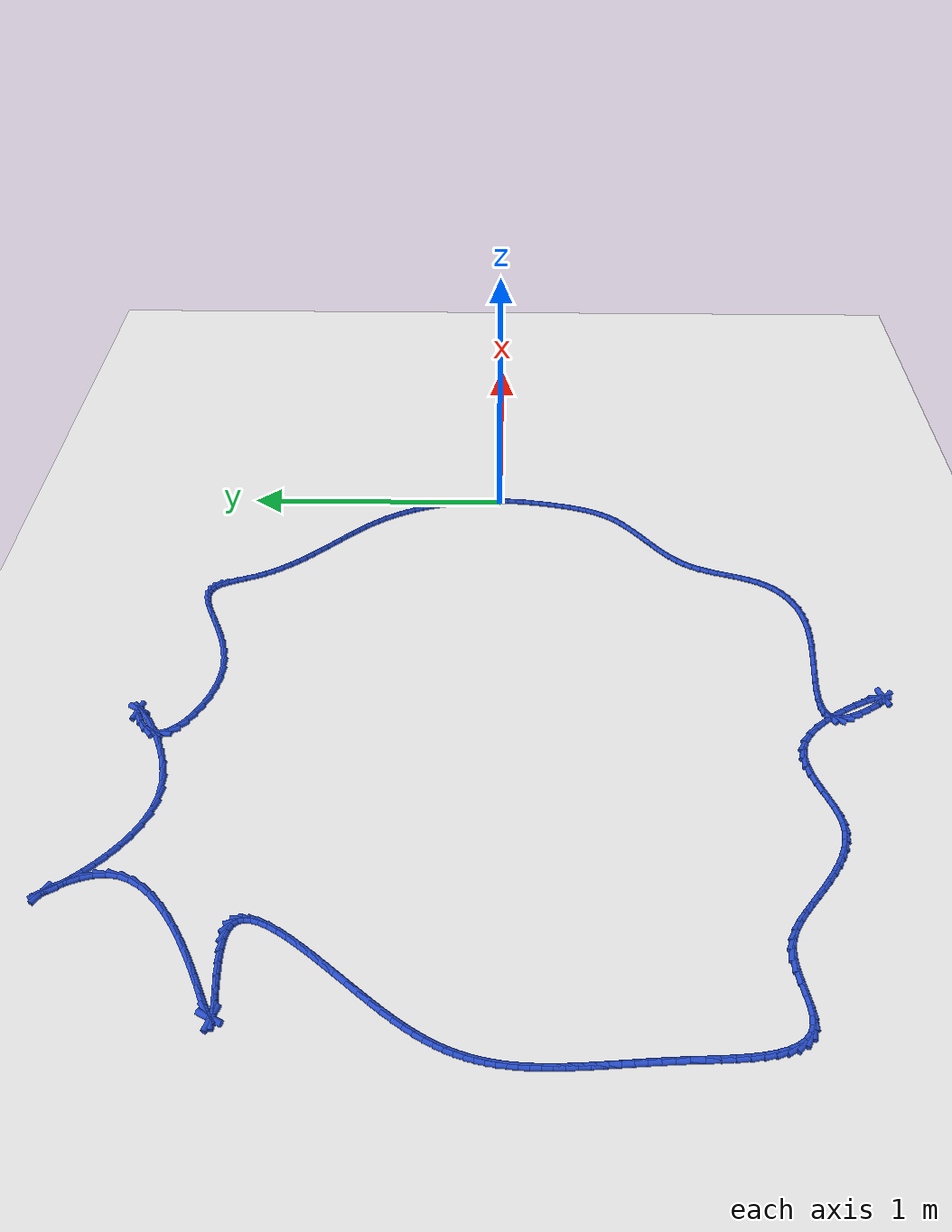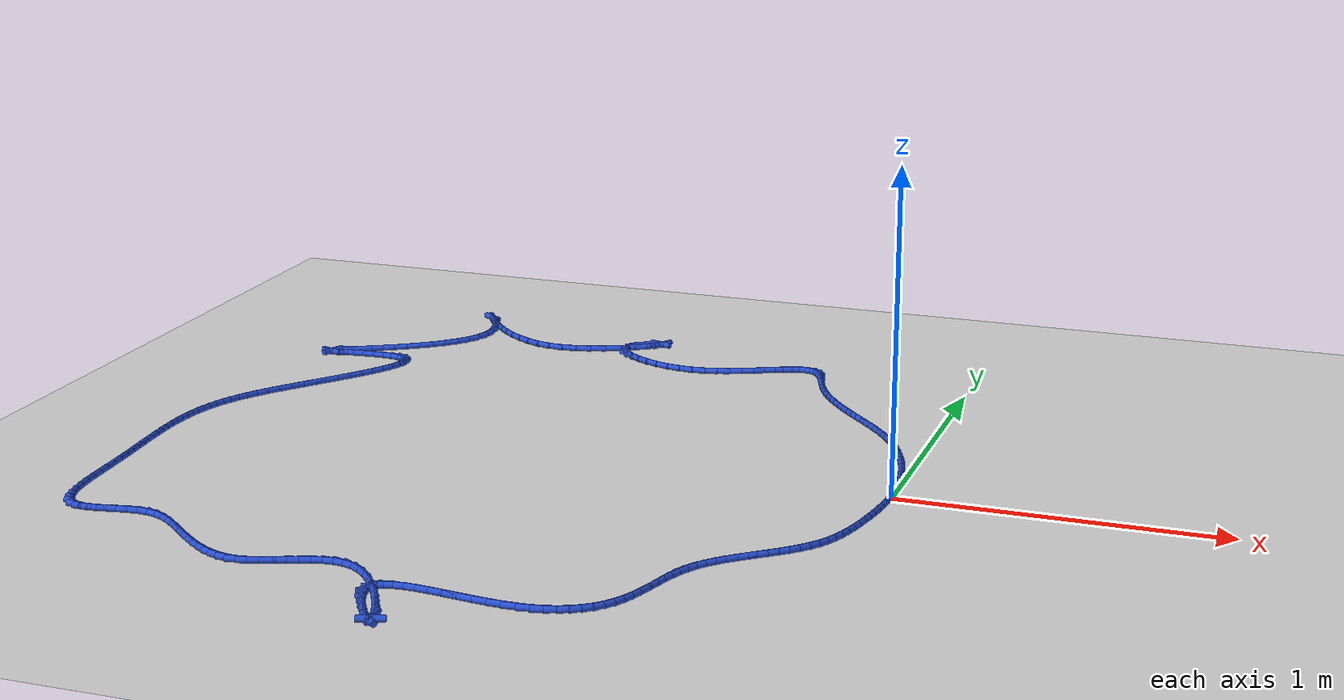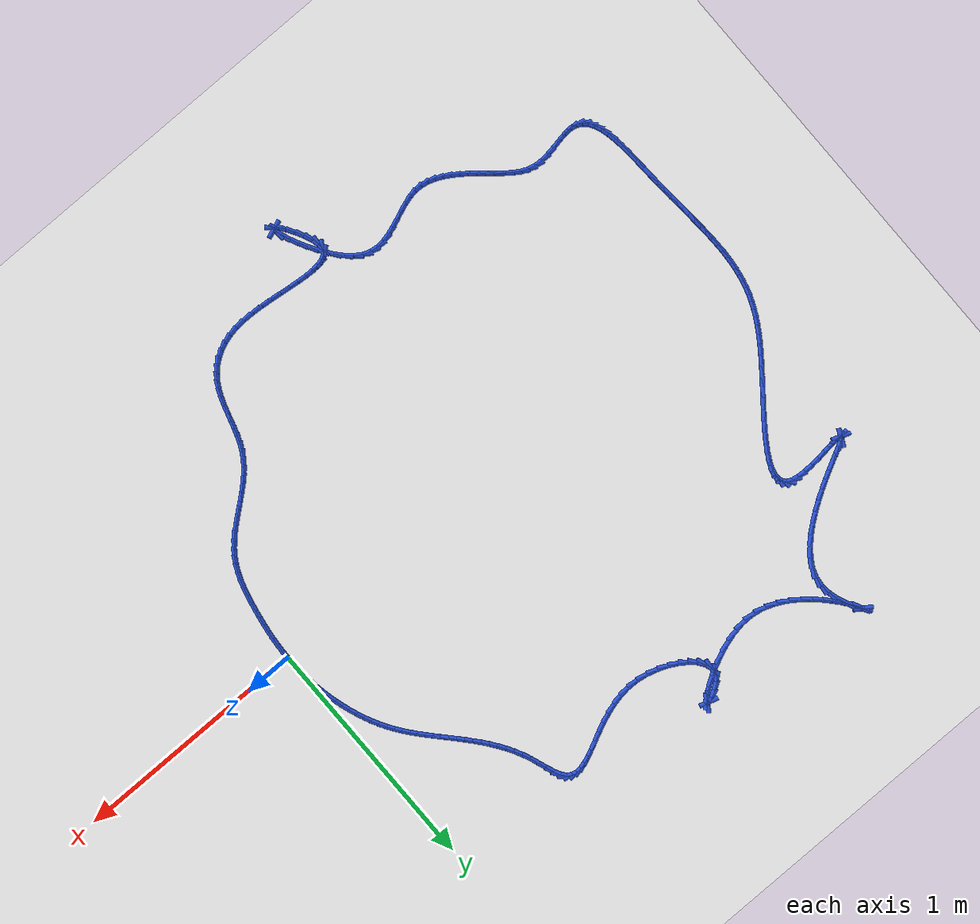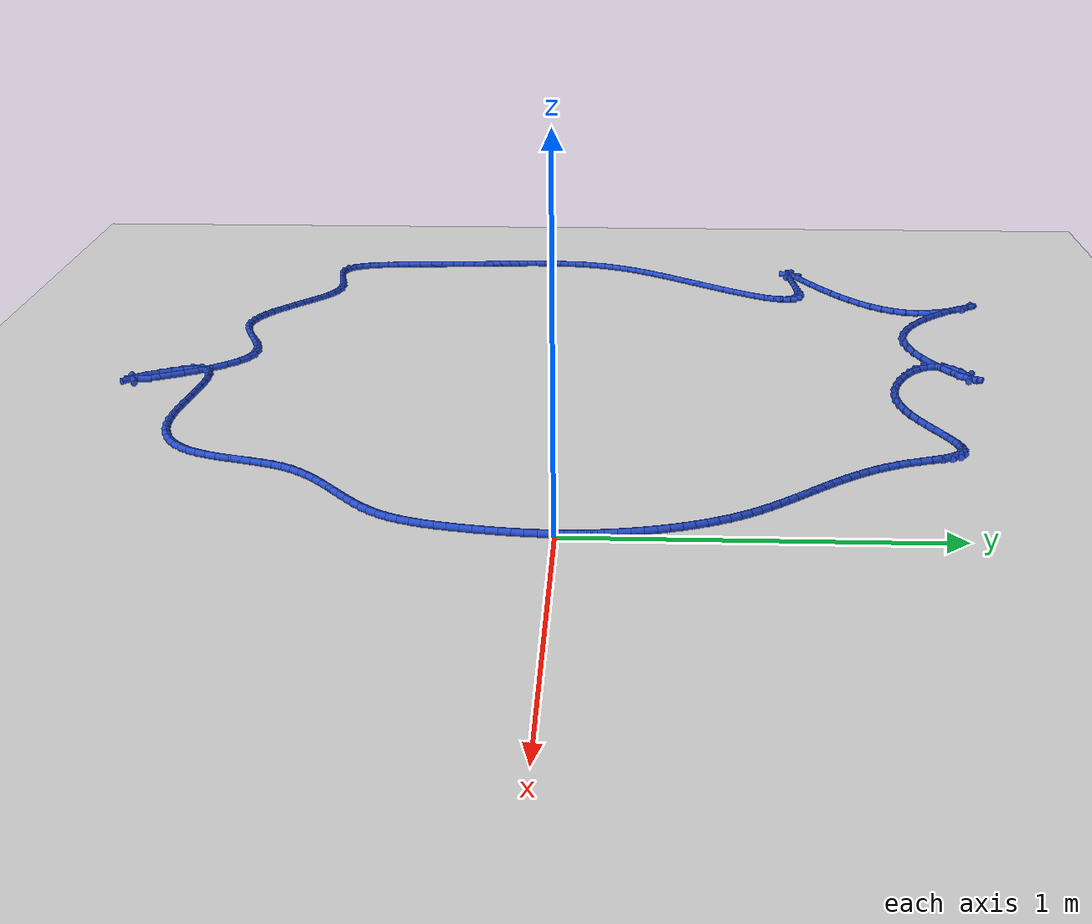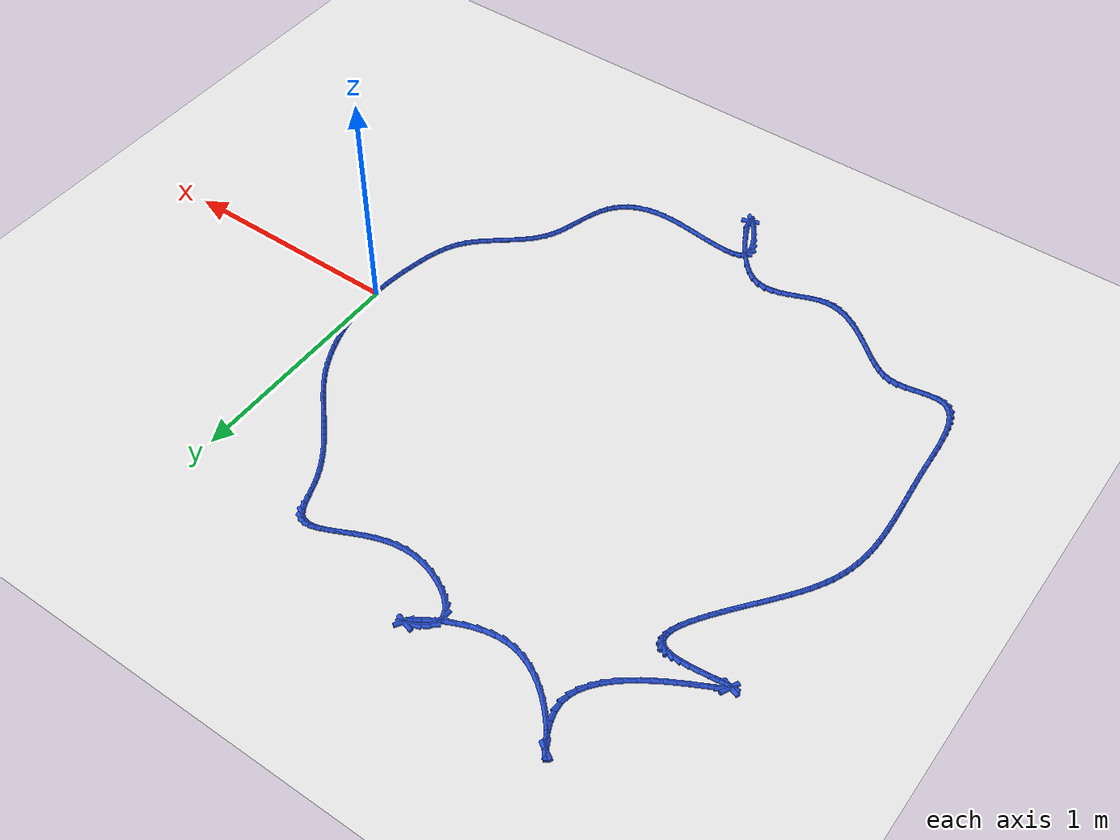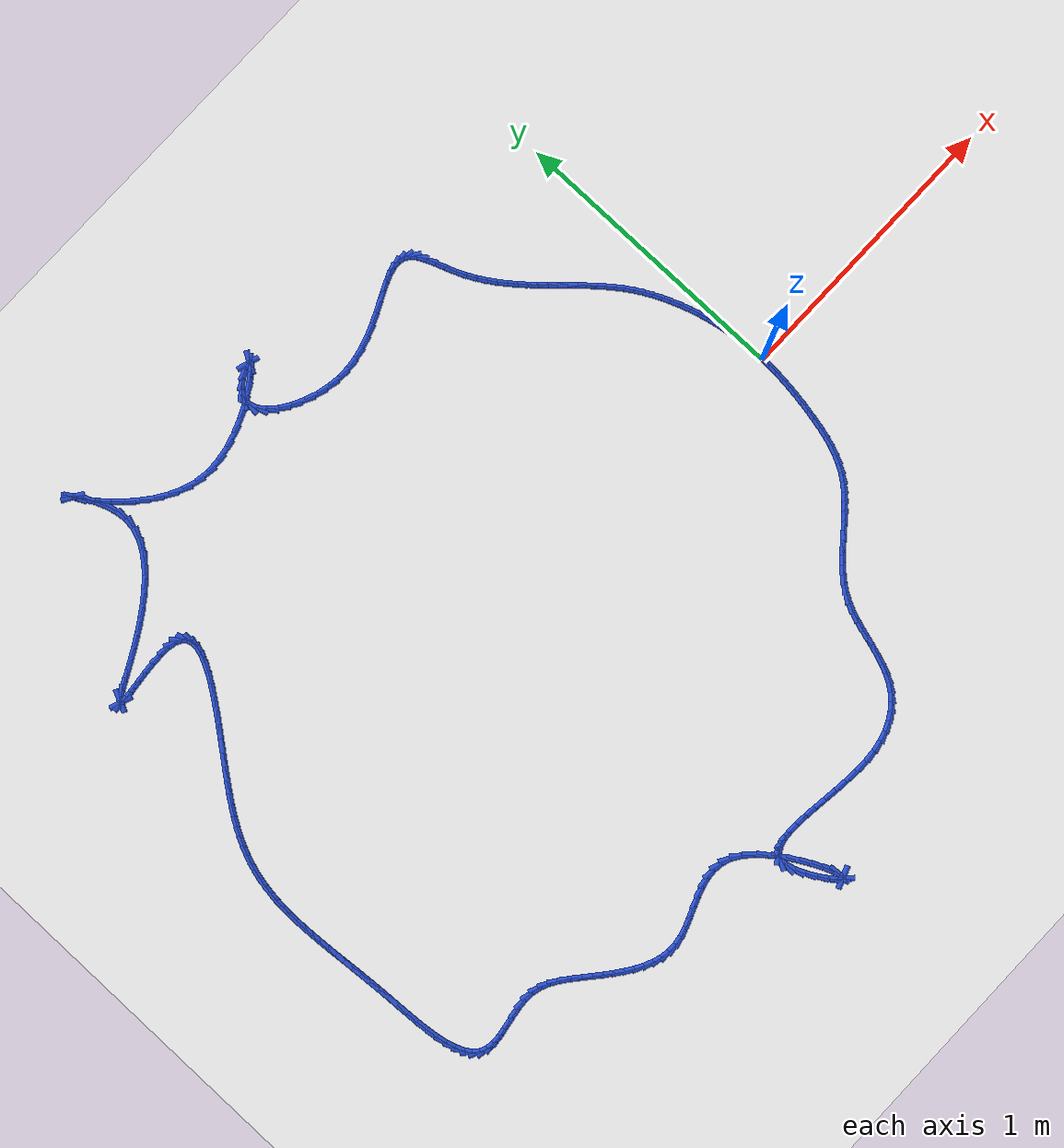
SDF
<sdf version="1.6">
 <world name="default">
  <light name="sun" type="directional">
   <pose>0 0 10 0 -0 0</pose>
   <diffuse>0.8 0.8 0.8 1</diffuse>
   <specular>0.2 0.2 0.2 1</specular>
   <attenuation>
    <range>1000</range>
    <constant>0.9</constant>
    <linear>0.01</linear>
    <quadratic>0.001</quadratic>
   </attenuation>
   <direction>-0.5 0.1 -0.9</direction>
  </light>
  <model name="ground_plane">
   <static>1</static>
   <link name="link">
    <collision name="collision">
     <geometry><plane><normal>0 0 1</normal><size>100 100</size></plane></geometry>
     <surface><friction><ode><mu>100</mu><mu2>50</mu2></ode></friction></surface>
    </collision>
    <visual name="visual">
     <cast_shadows>0</cast_shadows>
     <geometry><plane><normal>0 0 1</normal><size>100 100</size></plane></geometry>
     <material>
      <script><uri>file://media/materials/scripts/gazebo.material</uri><name>Gazebo/WhiteGlow</name></script>
     </material>
    </visual>
   </link>
  </model>
  <gravity>0 0 -9.8</gravity>
  <magnetic_field>6e-06 2.3e-05 -4.2e-05</magnetic_field>
  <atmosphere type="adiabatic"/>
  <physics name="default_physics" default="0" type="ode">
   <max_step_size>0.001</max_step_size>
   <real_time_factor>1</real_time_factor>
   <real_time_update_rate>1000</real_time_update_rate>
  </physics>
  <scene><ambient>0.4 0.4 0.4 1</ambient><background>0.7 0.7 0.7 1</background><shadows>1</shadows></scene>
  <spherical_coordinates>
   <surface_model>EARTH_WGS84</surface_model>
   <latitude_deg>0</latitude_deg>
   <longitude_deg>0</longitude_deg>
   <elevation>0</elevation>
   <heading_deg>0</heading_deg>
  </spherical_coordinates>
  <model name="line">
   <link name="link_0">
    <pose>0.0 -4.163336342344337e-17 0.01 0 1.57 -1.563006256594229</pose>
    <collision name="collision">
     <geometry><cylinder><radius>0.01</radius><length>0.08</length></cylinder></geometry>
    </collision>
    <visual name="visual">
     <material>
      <script><name>Gazebo/Blue</name><uri>file://media/materials/scripts/gazebo.material</uri></script>
     </material>
     <geometry><cylinder><radius>0.01</radius><length>0.08</length></cylinder></geometry>
    </visual>
   </link>
   <link name="link_1">
    <pose>-0.000248928956558965 0.0319540022993984 0.01 0 1.57 -1.5278305219193011</pose>
    <collision name="collision">
     <geometry><cylinder><radius>0.01</radius><length>0.08</length></cylinder></geometry>
    </collision>
    <visual name="visual">
     <material>
      <script><name>Gazebo/Blue</name><uri>file://media/materials/scripts/gazebo.material</uri></script>
     </material>
     <geometry><cylinder><radius>0.01</radius><length>0.08</length></cylinder></geometry>
    </visual>
   </link>
   <link name="link_2">
    <pose>-0.001624358744487196 0.0639464975463272 0.01 0 1.57 -1.492891923296698</pose>
    <collision name="collision">
     <geometry><cylinder><radius>0.01</radius><length>0.08</length></cylinder></geometry>
    </collision>
    <visual name="visual">
     <material>
      <script><name>Gazebo/Blue</name><uri>file://media/materials/scripts/gazebo.material</uri></script>
     </material>
     <geometry><cylinder><radius>0.01</radius><length>0.08</length></cylinder></geometry>
    </visual>
   </link>
   <link name="link_3">
    <pose>-0.0041220826799419075 0.09594300611781993 0.01 0 1.57 -1.4581609408207235</pose>
    <collision name="collision">
     <geometry><cylinder><radius>0.01</radius><length>0.08</length></cylinder></geometry>
    </collision>
    <visual name="visual">
     <material>
      <script><name>Gazebo/Blue</name><uri>file://media/materials/scripts/gazebo.material</uri></script>
     </material>
     <geometry><cylinder><radius>0.01</radius><length>0.08</length></cylinder></geometry>
    </visual>
   </link>
   <link name="link_4">
    <pose>-0.007737894079080308 0.1279090483909102 0.01 0 1.57 -1.423607430531382</pose>
    <collision name="collision">
     <geometry><cylinder><radius>0.01</radius><length>0.08</length></cylinder></geometry>
    </collision>
    <visual name="visual">
     <material>
      <script><name>Gazebo/Blue</name><uri>file://media/materials/scripts/gazebo.material</uri></script>
     </material>
     <geometry><cylinder><radius>0.01</radius><length>0.08</length></cylinder></geometry>
    </visual>
   </link>
   <link name="link_5">
    <pose>-0.012467586258059622 0.15981014474263164 0.01 0 1.57 -1.3892009409590484</pose>
    <collision name="collision">
     <geometry><cylinder><radius>0.01</radius><length>0.08</length></cylinder></geometry>
    </collision>
    <visual name="visual">
     <material>
      <script><name>Gazebo/Blue</name><uri>file://media/materials/scripts/gazebo.material</uri></script>
     </material>
     <geometry><cylinder><radius>0.01</radius><length>0.08</length></cylinder></geometry>
    </visual>
   </link>
   <link name="link_6">
    <pose>-0.01830695253303706 0.19161181555001774 0.01 0 1.57 -1.3549110092591592</pose>
    <collision name="collision">
     <geometry><cylinder><radius>0.01</radius><length>0.08</length></cylinder></geometry>
    </collision>
    <visual name="visual">
     <material>
      <script><name>Gazebo/Blue</name><uri>file://media/materials/scripts/gazebo.material</uri></script>
     </material>
     <geometry><cylinder><radius>0.01</radius><length>0.08</length></cylinder></geometry>
    </visual>
   </link>
   <link name="link_7">
    <pose>-0.02525178625785814 0.22327958102439927 0.01 0 1.57 -1.32052249762528</pose>
    <collision name="collision">
     <geometry><cylinder><radius>0.01</radius><length>0.08</length></cylinder></geometry>
    </collision>
    <visual name="visual">
     <material>
      <script><name>Gazebo/Blue</name><uri>file://media/materials/scripts/gazebo.material</uri></script>
     </material>
     <geometry><cylinder><radius>0.01</radius><length>0.08</length></cylinder></geometry>
    </visual>
   </link>
   <link name="link_8">
    <pose>-0.033300802831847345 0.25476611412608485 0.01 0 1.57 -1.2852364362277098</pose>
    <collision name="collision">
     <geometry><cylinder><radius>0.01</radius><length>0.08</length></cylinder></geometry>
    </collision>
    <visual name="visual">
     <material>
      <script><name>Gazebo/Blue</name><uri>file://media/materials/scripts/gazebo.material</uri></script>
     </material>
     <geometry><cylinder><radius>0.01</radius><length>0.08</length></cylinder></geometry>
    </visual>
   </link>
   <link name="link_9">
    <pose>-0.0424635939208002 0.2859762685303835 0.01 0 1.57 -1.2486706087328696</pose>
    <collision name="collision">
     <geometry><cylinder><radius>0.01</radius><length>0.08</length></cylinder></geometry>
    </collision>
    <visual name="visual">
     <material>
      <script><name>Gazebo/Blue</name><uri>file://media/materials/scripts/gazebo.material</uri></script>
     </material>
     <geometry><cylinder><radius>0.01</radius><length>0.08</length></cylinder></geometry>
    </visual>
   </link>
   <link name="link_10">
    <pose>-0.052752281195623335 0.31680377433120127 0.01 0 1.57 -1.2105892125753264</pose>
    <collision name="collision">
     <geometry><cylinder><radius>0.01</radius><length>0.08</length></cylinder></geometry>
    </collision>
    <visual name="visual">
     <material>
      <script><name>Gazebo/Blue</name><uri>file://media/materials/scripts/gazebo.material</uri></script>
     </material>
     <geometry><cylinder><radius>0.01</radius><length>0.08</length></cylinder></geometry>
    </visual>
   </link>
   <link name="link_11">
    <pose>-0.06417898632722333 0.3471423616224437 0.01 0 1.57 -1.1707524797545545</pose>
    <collision name="collision">
     <geometry><cylinder><radius>0.01</radius><length>0.08</length></cylinder></geometry>
    </collision>
    <visual name="visual">
     <material>
      <script><name>Gazebo/Blue</name><uri>file://media/materials/scripts/gazebo.material</uri></script>
     </material>
     <geometry><cylinder><radius>0.01</radius><length>0.08</length></cylinder></geometry>
    </visual>
   </link>
   <link name="link_12">
    <pose>-0.07675583098650679 0.3768857604980167 0.01 0 1.57 -1.1289172614760576</pose>
    <collision name="collision">
     <geometry><cylinder><radius>0.01</radius><length>0.08</length></cylinder></geometry>
    </collision>
    <visual name="visual">
     <material>
      <script><name>Gazebo/Blue</name><uri>file://media/materials/scripts/gazebo.material</uri></script>
     </material>
     <geometry><cylinder><radius>0.01</radius><length>0.08</length></cylinder></geometry>
    </visual>
   </link>
   <link name="link_13">
    <pose>-0.09049493684438034 0.405927701051826 0.01 0 1.57 -1.0848391326967213</pose>
    <collision name="collision">
     <geometry><cylinder><radius>0.01</radius><length>0.08</length></cylinder></geometry>
    </collision>
    <visual name="visual">
     <material>
      <script><name>Gazebo/Blue</name><uri>file://media/materials/scripts/gazebo.material</uri></script>
     </material>
     <geometry><cylinder><radius>0.01</radius><length>0.08</length></cylinder></geometry>
    </visual>
   </link>
   <link name="link_14">
    <pose>-0.10540842557175056 0.4341619133777777 0.01 0 1.57 -1.0382764347042215</pose>
    <collision name="collision">
     <geometry><cylinder><radius>0.01</radius><length>0.08</length></cylinder></geometry>
    </collision>
    <visual name="visual">
     <material>
      <script><name>Gazebo/Blue</name><uri>file://media/materials/scripts/gazebo.material</uri></script>
     </material>
     <geometry><cylinder><radius>0.01</radius><length>0.08</length></cylinder></geometry>
    </visual>
   </link>
   <link name="link_15">
    <pose>-0.12150841883952404 0.461482127569777 0.01 0 1.57 -0.9900257909279118</pose>
    <collision name="collision">
     <geometry><cylinder><radius>0.01</radius><length>0.08</length></cylinder></geometry>
    </collision>
    <visual name="visual">
     <material>
      <script><name>Gazebo/Blue</name><uri>file://media/materials/scripts/gazebo.material</uri></script>
     </material>
     <geometry><cylinder><radius>0.01</radius><length>0.08</length></cylinder></geometry>
    </visual>
   </link>
   <link name="link_16">
    <pose>-0.13878782946803 0.48781184397480276 0.01 0 1.57 -0.9459627137961062</pose>
    <collision name="collision">
     <geometry><cylinder><radius>0.01</radius><length>0.08</length></cylinder></geometry>
    </collision>
    <visual name="visual">
     <material>
      <script><name>Gazebo/Blue</name><uri>file://media/materials/scripts/gazebo.material</uri></script>
     </material>
     <geometry><cylinder><radius>0.01</radius><length>0.08</length></cylinder></geometry>
    </visual>
   </link>
   <link name="link_17">
    <pose>-0.15713027047494438 0.5132439579159979 0.01 0 1.57 -0.9085102322134792</pose>
    <collision name="collision">
     <geometry><cylinder><radius>0.01</radius><length>0.08</length></cylinder></geometry>
    </collision>
    <visual name="visual">
     <material>
      <script><name>Gazebo/Blue</name><uri>file://media/materials/scripts/gazebo.material</uri></script>
     </material>
     <geometry><cylinder><radius>0.01</radius><length>0.08</length></cylinder></geometry>
    </visual>
   </link>
   <link name="link_18">
    <pose>-0.17638074971390247 0.5379311957563047 0.01 0 1.57 -0.8779178885768317</pose>
    <collision name="collision">
     <geometry><cylinder><radius>0.01</radius><length>0.08</length></cylinder></geometry>
    </collision>
    <visual name="visual">
     <material>
      <script><name>Gazebo/Blue</name><uri>file://media/materials/scripts/gazebo.material</uri></script>
     </material>
     <geometry><cylinder><radius>0.01</radius><length>0.08</length></cylinder></geometry>
    </visual>
   </link>
   <link name="link_19">
    <pose>-0.1963842309153886 0.5620263522415894 0.01 0 1.57 -0.8543039969566919</pose>
    <collision name="collision">
     <geometry><cylinder><radius>0.01</radius><length>0.08</length></cylinder></geometry>
    </collision>
    <visual name="visual">
     <material>
      <script><name>Gazebo/Blue</name><uri>file://media/materials/scripts/gazebo.material</uri></script>
     </material>
     <geometry><cylinder><radius>0.01</radius><length>0.08</length></cylinder></geometry>
    </visual>
   </link>
   <link name="link_20">
    <pose>-0.21698567780988717 0.5856822221177187 0.01 0 1.57 -0.8376991096954095</pose>
    <collision name="collision">
     <geometry><cylinder><radius>0.01</radius><length>0.08</length></cylinder></geometry>
    </collision>
    <visual name="visual">
     <material>
      <script><name>Gazebo/Blue</name><uri>file://media/materials/scripts/gazebo.material</uri></script>
     </material>
     <geometry><cylinder><radius>0.01</radius><length>0.08</length></cylinder></geometry>
    </visual>
   </link>
   <link name="link_21">
    <pose>-0.23803005412788228 0.6090516001305586 0.01 0 1.57 -0.828080301824036</pose>
    <collision name="collision">
     <geometry><cylinder><radius>0.01</radius><length>0.08</length></cylinder></geometry>
    </collision>
    <visual name="visual">
     <material>
      <script><name>Gazebo/Blue</name><uri>file://media/materials/scripts/gazebo.material</uri></script>
     </material>
     <geometry><cylinder><radius>0.01</radius><length>0.08</length></cylinder></geometry>
    </visual>
   </link>
   <link name="link_22">
    <pose>-0.25936232359985834 0.6322872810259755 0.01 0 1.57 -0.8253959606728755</pose>
    <collision name="collision">
     <geometry><cylinder><radius>0.01</radius><length>0.08</length></cylinder></geometry>
    </collision>
    <visual name="visual">
     <material>
      <script><name>Gazebo/Blue</name><uri>file://media/materials/scripts/gazebo.material</uri></script>
     </material>
     <geometry><cylinder><radius>0.01</radius><length>0.08</length></cylinder></geometry>
    </visual>
   </link>
   <link name="link_23">
    <pose>-0.2808274499562997 0.6555420595498359 0.01 0 1.57 -0.8295802418904895</pose>
    <collision name="collision">
     <geometry><cylinder><radius>0.01</radius><length>0.08</length></cylinder></geometry>
    </collision>
    <visual name="visual">
     <material>
      <script><name>Gazebo/Blue</name><uri>file://media/materials/scripts/gazebo.material</uri></script>
     </material>
     <geometry><cylinder><radius>0.01</radius><length>0.08</length></cylinder></geometry>
    </visual>
   </link>
   <link name="link_24">
    <pose>-0.30227039692769053 0.6789687304480062 0.01 0 1.57 -0.8405573342523168</pose>
    <collision name="collision">
     <geometry><cylinder><radius>0.01</radius><length>0.08</length></cylinder></geometry>
    </collision>
    <visual name="visual">
     <material>
      <script><name>Gazebo/Blue</name><uri>file://media/materials/scripts/gazebo.material</uri></script>
     </material>
     <geometry><cylinder><radius>0.01</radius><length>0.08</length></cylinder></geometry>
    </visual>
   </link>
   <link name="link_25">
    <pose>-0.3235361282445152 0.7027200884663526 0.01 0 1.57 -0.8582361128925206</pose>
    <collision name="collision">
     <geometry><cylinder><radius>0.01</radius><length>0.08</length></cylinder></geometry>
    </collision>
    <visual name="visual">
     <material>
      <script><name>Gazebo/Blue</name><uri>file://media/materials/scripts/gazebo.material</uri></script>
     </material>
     <geometry><cylinder><radius>0.01</radius><length>0.08</length></cylinder></geometry>
    </visual>
   </link>
   <link name="link_26">
    <pose>-0.3444696076372581 0.7269489283507415 0.01 0 1.57 -0.8824960190921636</pose>
    <collision name="collision">
     <geometry><cylinder><radius>0.01</radius><length>0.08</length></cylinder></geometry>
    </collision>
    <visual name="visual">
     <material>
      <script><name>Gazebo/Blue</name><uri>file://media/materials/scripts/gazebo.material</uri></script>
     </material>
     <geometry><cylinder><radius>0.01</radius><length>0.08</length></cylinder></geometry>
    </visual>
   </link>
   <link name="link_27">
    <pose>-0.3649157988364032 0.7518080448470389 0.01 0 1.57 -0.9131654113348566</pose>
    <collision name="collision">
     <geometry><cylinder><radius>0.01</radius><length>0.08</length></cylinder></geometry>
    </collision>
    <visual name="visual">
     <material>
      <script><name>Gazebo/Blue</name><uri>file://media/materials/scripts/gazebo.material</uri></script>
     </material>
     <geometry><cylinder><radius>0.01</radius><length>0.08</length></cylinder></geometry>
    </visual>
   </link>
   <link name="link_28">
    <pose>-0.3847196655724351 0.7774502327011117 0.01 0 1.57 -0.9499944257599731</pose>
    <collision name="collision">
     <geometry><cylinder><radius>0.01</radius><length>0.08</length></cylinder></geometry>
    </collision>
    <visual name="visual">
     <material>
      <script><name>Gazebo/Blue</name><uri>file://media/materials/scripts/gazebo.material</uri></script>
     </material>
     <geometry><cylinder><radius>0.01</radius><length>0.08</length></cylinder></geometry>
    </visual>
   </link>
   <link name="link_29">
    <pose>-0.403726171575838 0.8040282866588262 0.01 0 1.57 -0.9926256515100144</pose>
    <collision name="collision">
     <geometry><cylinder><radius>0.01</radius><length>0.08</length></cylinder></geometry>
    </collision>
    <visual name="visual">
     <material>
      <script><name>Gazebo/Blue</name><uri>file://media/materials/scripts/gazebo.material</uri></script>
     </material>
     <geometry><cylinder><radius>0.01</radius><length>0.08</length></cylinder></geometry>
    </visual>
   </link>
   <link name="link_30">
    <pose>-0.4217802805770962 0.8316950014660482 0.01 0 1.57 -1.0405675045535012</pose>
    <collision name="collision">
     <geometry><cylinder><radius>0.01</radius><length>0.08</length></cylinder></geometry>
    </collision>
    <visual name="visual">
     <material>
      <script><name>Gazebo/Blue</name><uri>file://media/materials/scripts/gazebo.material</uri></script>
     </material>
     <geometry><cylinder><radius>0.01</radius><length>0.08</length></cylinder></geometry>
    </visual>
   </link>
   <link name="link_31">
    <pose>-0.4387269563066942 0.8606031718686451 0.01 0 1.57 -1.0931765645615352</pose>
    <collision name="collision">
     <geometry><cylinder><radius>0.01</radius><length>0.08</length></cylinder></geometry>
    </collision>
    <visual name="visual">
     <material>
      <script><name>Gazebo/Blue</name><uri>file://media/materials/scripts/gazebo.material</uri></script>
     </material>
     <geometry><cylinder><radius>0.01</radius><length>0.08</length></cylinder></geometry>
    </visual>
   </link>
   <link name="link_32">
    <pose>-0.454411162495116 0.890905592612482 0.01 0 1.57 -1.1496554937154349</pose>
    <collision name="collision">
     <geometry><cylinder><radius>0.01</radius><length>0.08</length></cylinder></geometry>
    </collision>
    <visual name="visual">
     <material>
      <script><name>Gazebo/Blue</name><uri>file://media/materials/scripts/gazebo.material</uri></script>
     </material>
     <geometry><cylinder><radius>0.01</radius><length>0.08</length></cylinder></geometry>
    </visual>
   </link>
   <link name="link_33">
    <pose>-0.4686778628728458 0.9227550584434259 0.01 0 1.57 -1.2042232651507694</pose>
    <collision name="collision">
     <geometry><cylinder><radius>0.01</radius><length>0.08</length></cylinder></geometry>
    </collision>
    <visual name="visual">
     <material>
      <script><name>Gazebo/Blue</name><uri>file://media/materials/scripts/gazebo.material</uri></script>
     </material>
     <geometry><cylinder><radius>0.01</radius><length>0.08</length></cylinder></geometry>
    </visual>
   </link>
   <link name="link_34">
    <pose>-0.4814732199996808 0.9560827321562883 0.01 0 1.57 -1.2240359930948945</pose>
    <collision name="collision">
     <geometry><cylinder><radius>0.01</radius><length>0.08</length></cylinder></geometry>
    </collision>
    <visual name="visual">
     <material>
      <script><name>Gazebo/Blue</name><uri>file://media/materials/scripts/gazebo.material</uri></script>
     </material>
     <geometry><cylinder><radius>0.01</radius><length>0.08</length></cylinder></geometry>
    </visual>
   </link>
   <link name="link_35">
    <pose>-0.49345928894048247 0.989251925872889 0.01 0 1.57 -1.1939898592686213</pose>
    <collision name="collision">
     <geometry><cylinder><radius>0.01</radius><length>0.08</length></cylinder></geometry>
    </collision>
    <visual name="visual">
     <material>
      <script><name>Gazebo/Blue</name><uri>file://media/materials/scripts/gazebo.material</uri></script>
     </material>
     <geometry><cylinder><radius>0.01</radius><length>0.08</length></cylinder></geometry>
    </visual>
   </link>
   <link name="link_36">
    <pose>-0.5056068714079089 1.0199497766802443 0.01 0 1.57 -1.097145835350373</pose>
    <collision name="collision">
     <geometry><cylinder><radius>0.01</radius><length>0.08</length></cylinder></geometry>
    </collision>
    <visual name="visual">
     <material>
      <script><name>Gazebo/Blue</name><uri>file://media/materials/scripts/gazebo.material</uri></script>
     </material>
     <geometry><cylinder><radius>0.01</radius><length>0.08</length></cylinder></geometry>
    </visual>
   </link>
   <link name="link_37">
    <pose>-0.5188879838372248 1.045860761344658 0.01 0 1.57 -0.887082022074926</pose>
    <collision name="collision">
     <geometry><cylinder><radius>0.01</radius><length>0.08</length></cylinder></geometry>
    </collision>
    <visual name="visual">
     <material>
      <script><name>Gazebo/Blue</name><uri>file://media/materials/scripts/gazebo.material</uri></script>
     </material>
     <geometry><cylinder><radius>0.01</radius><length>0.08</length></cylinder></geometry>
    </visual>
   </link>
   <link name="link_38">
    <pose>-0.5342574480073634 1.0647230932263498 0.01 0 1.57 -0.5526281072199354</pose>
    <collision name="collision">
     <geometry><cylinder><radius>0.01</radius><length>0.08</length></cylinder></geometry>
    </collision>
    <visual name="visual">
     <material>
      <script><name>Gazebo/Blue</name><uri>file://media/materials/scripts/gazebo.material</uri></script>
     </material>
     <geometry><cylinder><radius>0.01</radius><length>0.08</length></cylinder></geometry>
    </visual>
   </link>
   <link name="link_39">
    <pose>-0.5521880657098341 1.0757813904558735 0.01 0 1.57 -0.20149169539810724</pose>
    <collision name="collision">
     <geometry><cylinder><radius>0.01</radius><length>0.08</length></cylinder></geometry>
    </collision>
    <visual name="visual">
     <material>
      <script><name>Gazebo/Blue</name><uri>file://media/materials/scripts/gazebo.material</uri></script>
     </material>
     <geometry><cylinder><radius>0.01</radius><length>0.08</length></cylinder></geometry>
    </visual>
   </link>
   <link name="link_40">
    <pose>-0.5726169906189474 1.079954274109767 0.01 0 1.57 0.0745900186100927</pose>
    <collision name="collision">
     <geometry><cylinder><radius>0.01</radius><length>0.08</length></cylinder></geometry>
    </collision>
    <visual name="visual">
     <material>
      <script><name>Gazebo/Blue</name><uri>file://media/materials/scripts/gazebo.material</uri></script>
     </material>
     <geometry><cylinder><radius>0.01</radius><length>0.08</length></cylinder></geometry>
    </visual>
   </link>
   <link name="link_41">
    <pose>-0.5954534186957834 1.0782477384724785 0.01 0 1.57 0.25586253684193516</pose>
    <collision name="collision">
     <geometry><cylinder><radius>0.01</radius><length>0.08</length></cylinder></geometry>
    </collision>
    <visual name="visual">
     <material>
      <script><name>Gazebo/Blue</name><uri>file://media/materials/scripts/gazebo.material</uri></script>
     </material>
     <geometry><cylinder><radius>0.01</radius><length>0.08</length></cylinder></geometry>
    </visual>
   </link>
   <link name="link_42">
    <pose>-0.6206065459014207 1.0716677778284585 0.01 0 1.57 0.3645302382293565</pose>
    <collision name="collision">
     <geometry><cylinder><radius>0.01</radius><length>0.08</length></cylinder></geometry>
    </collision>
    <visual name="visual">
     <material>
      <script><name>Gazebo/Blue</name><uri>file://media/materials/scripts/gazebo.material</uri></script>
     </material>
     <geometry><cylinder><radius>0.01</radius><length>0.08</length></cylinder></geometry>
    </visual>
   </link>
   <link name="link_43">
    <pose>-0.6479855681969392 1.0612203864621559 0.01 0 1.57 0.4236278530203895</pose>
    <collision name="collision">
     <geometry><cylinder><radius>0.01</radius><length>0.08</length></cylinder></geometry>
    </collision>
    <visual name="visual">
     <material>
      <script><name>Gazebo/Blue</name><uri>file://media/materials/scripts/gazebo.material</uri></script>
     </material>
     <geometry><cylinder><radius>0.01</radius><length>0.08</length></cylinder></geometry>
    </visual>
   </link>
   <link name="link_44">
    <pose>-0.6774996815434189 1.047911558658021 0.01 0 1.57 0.4479380733620824</pose>
    <collision name="collision">
     <geometry><cylinder><radius>0.01</radius><length>0.08</length></cylinder></geometry>
    </collision>
    <visual name="visual">
     <material>
      <script><name>Gazebo/Blue</name><uri>file://media/materials/scripts/gazebo.material</uri></script>
     </material>
     <geometry><cylinder><radius>0.01</radius><length>0.08</length></cylinder></geometry>
    </visual>
   </link>
   <link name="link_45">
    <pose>-0.7090580819019382 1.0327472887005027 0.01 0 1.57 0.44577267475583565</pose>
    <collision name="collision">
     <geometry><cylinder><radius>0.01</radius><length>0.08</length></cylinder></geometry>
    </collision>
    <visual name="visual">
     <material>
      <script><name>Gazebo/Blue</name><uri>file://media/materials/scripts/gazebo.material</uri></script>
     </material>
     <geometry><cylinder><radius>0.01</radius><length>0.08</length></cylinder></geometry>
    </visual>
   </link>
   <link name="link_46">
    <pose>-0.7425699652335775 1.0167335708740508 0.01 0 1.57 0.42141000356976116</pose>
    <collision name="collision">
     <geometry><cylinder><radius>0.01</radius><length>0.08</length></cylinder></geometry>
    </collision>
    <visual name="visual">
     <material>
      <script><name>Gazebo/Blue</name><uri>file://media/materials/scripts/gazebo.material</uri></script>
     </material>
     <geometry><cylinder><radius>0.01</radius><length>0.08</length></cylinder></geometry>
    </visual>
   </link>
   <link name="link_47">
    <pose>-0.7779445274994157 1.0008763994631151 0.01 0 1.57 0.3766958932644989</pose>
    <collision name="collision">
     <geometry><cylinder><radius>0.01</radius><length>0.08</length></cylinder></geometry>
    </collision>
    <visual name="visual">
     <material>
      <script><name>Gazebo/Blue</name><uri>file://media/materials/scripts/gazebo.material</uri></script>
     </material>
     <geometry><cylinder><radius>0.01</radius><length>0.08</length></cylinder></geometry>
    </visual>
   </link>
   <link name="link_48">
    <pose>-0.8150909646605328 0.9861817687521451 0.01 0 1.57 0.3120676215993677</pose>
    <collision name="collision">
     <geometry><cylinder><radius>0.01</radius><length>0.08</length></cylinder></geometry>
    </collision>
    <visual name="visual">
     <material>
      <script><name>Gazebo/Blue</name><uri>file://media/materials/scripts/gazebo.material</uri></script>
     </material>
     <geometry><cylinder><radius>0.01</radius><length>0.08</length></cylinder></geometry>
    </visual>
   </link>
   <link name="link_49">
    <pose>-0.8539184726780076 0.9736556730255902 0.01 0 1.57 0.22737165304087853</pose>
    <collision name="collision">
     <geometry><cylinder><radius>0.01</radius><length>0.08</length></cylinder></geometry>
    </collision>
    <visual name="visual">
     <material>
      <script><name>Gazebo/Blue</name><uri>file://media/materials/scripts/gazebo.material</uri></script>
     </material>
     <geometry><cylinder><radius>0.01</radius><length>0.08</length></cylinder></geometry>
    </visual>
   </link>
   <link name="link_50">
    <pose>-0.8943362475129205 0.9643041065678999 0.01 0 1.57 0.1227430136782317</pose>
    <collision name="collision">
     <geometry><cylinder><radius>0.01</radius><length>0.08</length></cylinder></geometry>
    </collision>
    <visual name="visual">
     <material>
      <script><name>Gazebo/Blue</name><uri>file://media/materials/scripts/gazebo.material</uri></script>
     </material>
     <geometry><cylinder><radius>0.01</radius><length>0.08</length></cylinder></geometry>
    </visual>
   </link>
   <link name="link_51">
    <pose>-0.9362534851263498 0.9591330636635236 0.01 0 1.57 -0.00035717513155542773</pose>
    <collision name="collision">
     <geometry><cylinder><radius>0.01</radius><length>0.08</length></cylinder></geometry>
    </collision>
    <visual name="visual">
     <material>
      <script><name>Gazebo/Blue</name><uri>file://media/materials/scripts/gazebo.material</uri></script>
     </material>
     <geometry><cylinder><radius>0.01</radius><length>0.08</length></cylinder></geometry>
    </visual>
   </link>
   <link name="link_52">
    <pose>-0.9795793814793761 0.9591485385969113 0.01 0 1.57 -0.13365852641760356</pose>
    <collision name="collision">
     <geometry><cylinder><radius>0.01</radius><length>0.08</length></cylinder></geometry>
    </collision>
    <visual name="visual">
     <material>
      <script><name>Gazebo/Blue</name><uri>file://media/materials/scripts/gazebo.material</uri></script>
     </material>
     <geometry><cylinder><radius>0.01</radius><length>0.08</length></cylinder></geometry>
    </visual>
   </link>
   <link name="link_53">
    <pose>-1.0240331504240434 0.9651258001099841 0.01 0 1.57 -0.25368828305376373</pose>
    <collision name="collision">
     <geometry><cylinder><radius>0.01</radius><length>0.08</length></cylinder></geometry>
    </collision>
    <visual name="visual">
     <material>
      <script><name>Gazebo/Blue</name><uri>file://media/materials/scripts/gazebo.material</uri></script>
     </material>
     <geometry><cylinder><radius>0.01</radius><length>0.08</length></cylinder></geometry>
    </visual>
   </link>
   <link name="link_54">
    <pose>-1.0683195794695923 0.9766081374204405 0.01 0 1.57 -0.362658353411377</pose>
    <collision name="collision">
     <geometry><cylinder><radius>0.01</radius><length>0.08</length></cylinder></geometry>
    </collision>
    <visual name="visual">
     <material>
      <script><name>Gazebo/Blue</name><uri>file://media/materials/scripts/gazebo.material</uri></script>
     </material>
     <geometry><cylinder><radius>0.01</radius><length>0.08</length></cylinder></geometry>
    </visual>
   </link>
   <link name="link_55">
    <pose>-1.1108062508050187 0.9927293176028048 0.01 0 1.57 -0.47112447422631526</pose>
    <collision name="collision">
     <geometry><cylinder><radius>0.01</radius><length>0.08</length></cylinder></geometry>
    </collision>
    <visual name="visual">
     <material>
      <script><name>Gazebo/Blue</name><uri>file://media/materials/scripts/gazebo.material</uri></script>
     </material>
     <geometry><cylinder><radius>0.01</radius><length>0.08</length></cylinder></geometry>
    </visual>
   </link>
   <link name="link_56">
    <pose>-1.149860520837305 1.0126228335285312 0.01 0 1.57 -0.5908459494556867</pose>
    <collision name="collision">
     <geometry><cylinder><radius>0.01</radius><length>0.08</length></cylinder></geometry>
    </collision>
    <visual name="visual">
     <material>
      <script><name>Gazebo/Blue</name><uri>file://media/materials/scripts/gazebo.material</uri></script>
     </material>
     <geometry><cylinder><radius>0.01</radius><length>0.08</length></cylinder></geometry>
    </visual>
   </link>
   <link name="link_57">
    <pose>-1.1838497459734345 1.0354221780690747 0.01 0 1.57 -0.7383800681940237</pose>
    <collision name="collision">
     <geometry><cylinder><radius>0.01</radius><length>0.08</length></cylinder></geometry>
    </collision>
    <visual name="visual">
     <material>
      <script><name>Gazebo/Blue</name><uri>file://media/materials/scripts/gazebo.material</uri></script>
     </material>
     <geometry><cylinder><radius>0.01</radius><length>0.08</length></cylinder></geometry>
    </visual>
   </link>
   <link name="link_58">
    <pose>-1.2111412826203907 1.0602608440958892 0.01 0 1.57 -0.9409004756554119</pose>
    <collision name="collision">
     <geometry><cylinder><radius>0.01</radius><length>0.08</length></cylinder></geometry>
    </collision>
    <visual name="visual">
     <material>
      <script><name>Gazebo/Blue</name><uri>file://media/materials/scripts/gazebo.material</uri></script>
     </material>
     <geometry><cylinder><radius>0.01</radius><length>0.08</length></cylinder></geometry>
    </visual>
   </link>
   <link name="link_59">
    <pose>-1.230102487185157 1.0862723244804307 0.01 0 1.57 -1.241349655963164</pose>
    <collision name="collision">
     <geometry><cylinder><radius>0.01</radius><length>0.08</length></cylinder></geometry>
    </collision>
    <visual name="visual">
     <material>
      <script><name>Gazebo/Blue</name><uri>file://media/materials/scripts/gazebo.material</uri></script>
     </material>
     <geometry><cylinder><radius>0.01</radius><length>0.08</length></cylinder></geometry>
    </visual>
   </link>
   <link name="link_60">
    <pose>-1.2391007160747158 1.1125901120941528 0.01 0 1.57 1.470296243678676</pose>
    <collision name="collision">
     <geometry><cylinder><radius>0.01</radius><length>0.08</length></cylinder></geometry>
    </collision>
    <visual name="visual">
     <material>
      <script><name>Gazebo/Blue</name><uri>file://media/materials/scripts/gazebo.material</uri></script>
     </material>
     <geometry><cylinder><radius>0.01</radius><length>0.08</length></cylinder></geometry>
    </visual>
   </link>
   <link name="link_61">
    <pose>-1.2365033256960516 1.138347699808511 0.01 0 1.57 0.9944003443232351</pose>
    <collision name="collision">
     <geometry><cylinder><radius>0.01</radius><length>0.08</length></cylinder></geometry>
    </collision>
    <visual name="visual">
     <material>
      <script><name>Gazebo/Blue</name><uri>file://media/materials/scripts/gazebo.material</uri></script>
     </material>
     <geometry><cylinder><radius>0.01</radius><length>0.08</length></cylinder></geometry>
    </visual>
   </link>
   <link name="link_62">
    <pose>-1.2206887707183847 1.1626766789490872 0.01 0 1.57 0.6666134272885653</pose>
    <collision name="collision">
     <geometry><cylinder><radius>0.01</radius><length>0.08</length></cylinder></geometry>
    </collision>
    <visual name="visual">
     <material>
      <script><name>Gazebo/Blue</name><uri>file://media/materials/scripts/gazebo.material</uri></script>
     </material>
     <geometry><cylinder><radius>0.01</radius><length>0.08</length></cylinder></geometry>
    </visual>
   </link>
   <link name="link_63">
    <pose>-1.19342295070974 1.1841282453051103 0.01 0 1.57 0.4997919217530542</pose>
    <collision name="collision">
     <geometry><cylinder><radius>0.01</radius><length>0.08</length></cylinder></geometry>
    </collision>
    <visual name="visual">
     <material>
      <script><name>Gazebo/Blue</name><uri>file://media/materials/scripts/gazebo.material</uri></script>
     </material>
     <geometry><cylinder><radius>0.01</radius><length>0.08</length></cylinder></geometry>
    </visual>
   </link>
   <link name="link_64">
    <pose>-1.164614901225209 1.199858372036359 0.01 0 1.57 0.347324865897253</pose>
    <collision name="collision">
     <geometry><cylinder><radius>0.01</radius><length>0.08</length></cylinder></geometry>
    </collision>
    <visual name="visual">
     <material>
      <script><name>Gazebo/Blue</name><uri>file://media/materials/scripts/gazebo.material</uri></script>
     </material>
     <geometry><cylinder><radius>0.01</radius><length>0.08</length></cylinder></geometry>
    </visual>
   </link>
   <link name="link_65">
    <pose>-1.144956734683563 1.2069746255836111 0.01 0 1.57 -0.2845978343237876</pose>
    <collision name="collision">
     <geometry><cylinder><radius>0.01</radius><length>0.08</length></cylinder></geometry>
    </collision>
    <visual name="visual">
     <material>
      <script><name>Gazebo/Blue</name><uri>file://media/materials/scripts/gazebo.material</uri></script>
     </material>
     <geometry><cylinder><radius>0.01</radius><length>0.08</length></cylinder></geometry>
    </visual>
   </link>
   <link name="link_66">
    <pose>-1.1385105055588038 1.2050888523621355 0.01 0 1.57 1.0347167951568164</pose>
    <collision name="collision">
     <geometry><cylinder><radius>0.01</radius><length>0.08</length></cylinder></geometry>
    </collision>
    <visual name="visual">
     <material>
      <script><name>Gazebo/Blue</name><uri>file://media/materials/scripts/gazebo.material</uri></script>
     </material>
     <geometry><cylinder><radius>0.01</radius><length>0.08</length></cylinder></geometry>
    </visual>
   </link>
   <link name="link_67">
    <pose>-1.144015157053873 1.1958235238932209 0.01 0 1.57 0.7506302580921321</pose>
    <collision name="collision">
     <geometry><cylinder><radius>0.01</radius><length>0.08</length></cylinder></geometry>
    </collision>
    <visual name="visual">
     <material>
      <script><name>Gazebo/Blue</name><uri>file://media/materials/scripts/gazebo.material</uri></script>
     </material>
     <geometry><cylinder><radius>0.01</radius><length>0.08</length></cylinder></geometry>
    </visual>
   </link>
   <link name="link_68">
    <pose>-1.160059414456606 1.180857851431012 0.01 0 1.57 0.6462251928461011</pose>
    <collision name="collision">
     <geometry><cylinder><radius>0.01</radius><length>0.08</length></cylinder></geometry>
    </collision>
    <visual name="visual">
     <material>
      <script><name>Gazebo/Blue</name><uri>file://media/materials/scripts/gazebo.material</uri></script>
     </material>
     <geometry><cylinder><radius>0.01</radius><length>0.08</length></cylinder></geometry>
    </visual>
   </link>
   <link name="link_69">
    <pose>-1.1852320030548371 1.1618710462296538 0.01 0 1.57 0.5753155610667714</pose>
    <collision name="collision">
     <geometry><cylinder><radius>0.01</radius><length>0.08</length></cylinder></geometry>
    </collision>
    <visual name="visual">
     <material>
      <script><name>Gazebo/Blue</name><uri>file://media/materials/scripts/gazebo.material</uri></script>
     </material>
     <geometry><cylinder><radius>0.01</radius><length>0.08</length></cylinder></geometry>
    </visual>
   </link>
   <link name="link_70">
    <pose>-1.2181216481364012 1.1405423195432907 0.01 0 1.57 0.5113036462322049</pose>
    <collision name="collision">
     <geometry><cylinder><radius>0.01</radius><length>0.08</length></cylinder></geometry>
    </collision>
    <visual name="visual">
     <material>
      <script><name>Gazebo/Blue</name><uri>file://media/materials/scripts/gazebo.material</uri></script>
     </material>
     <geometry><cylinder><radius>0.01</radius><length>0.08</length></cylinder></geometry>
    </visual>
   </link>
   <link name="link_71">
    <pose>-1.2573170749891327 1.1185508826260684 0.01 0 1.57 0.4440443674464038</pose>
    <collision name="collision">
     <geometry><cylinder><radius>0.01</radius><length>0.08</length></cylinder></geometry>
    </collision>
    <visual name="visual">
     <material>
      <script><name>Gazebo/Blue</name><uri>file://media/materials/scripts/gazebo.material</uri></script>
     </material>
     <geometry><cylinder><radius>0.01</radius><length>0.08</length></cylinder></geometry>
    </visual>
   </link>
   <link name="link_72">
    <pose>-1.3014070089008665 1.0975759467321315 0.01 0 1.57 0.3668414746243127</pose>
    <collision name="collision">
     <geometry><cylinder><radius>0.01</radius><length>0.08</length></cylinder></geometry>
    </collision>
    <visual name="visual">
     <material>
      <script><name>Gazebo/Blue</name><uri>file://media/materials/scripts/gazebo.material</uri></script>
     </material>
     <geometry><cylinder><radius>0.01</radius><length>0.08</length></cylinder></geometry>
    </visual>
   </link>
   <link name="link_73">
    <pose>-1.3489801751594384 1.0792967231156254 0.01 0 1.57 0.27307716609180765</pose>
    <collision name="collision">
     <geometry><cylinder><radius>0.01</radius><length>0.08</length></cylinder></geometry>
    </collision>
    <visual name="visual">
     <material>
      <script><name>Gazebo/Blue</name><uri>file://media/materials/scripts/gazebo.material</uri></script>
     </material>
     <geometry><cylinder><radius>0.01</radius><length>0.08</length></cylinder></geometry>
    </visual>
   </link>
   <link name="link_74">
    <pose>-1.3986252990526813 1.0653924230306946 0.01 0 1.57 0.15480041851237744</pose>
    <collision name="collision">
     <geometry><cylinder><radius>0.01</radius><length>0.08</length></cylinder></geometry>
    </collision>
    <visual name="visual">
     <material>
      <script><name>Gazebo/Blue</name><uri>file://media/materials/scripts/gazebo.material</uri></script>
     </material>
     <geometry><cylinder><radius>0.01</radius><length>0.08</length></cylinder></geometry>
    </visual>
   </link>
   <link name="link_75">
    <pose>-1.4489311058684309 1.0575422577314844 0.01 0 1.57 0.0023984486746303924</pose>
    <collision name="collision">
     <geometry><cylinder><radius>0.01</radius><length>0.08</length></cylinder></geometry>
    </collision>
    <visual name="visual">
     <material>
      <script><name>Gazebo/Blue</name><uri>file://media/materials/scripts/gazebo.material</uri></script>
     </material>
     <geometry><cylinder><radius>0.01</radius><length>0.08</length></cylinder></geometry>
    </visual>
   </link>
   <link name="link_76">
    <pose>-1.4984870153752496 1.057423400198096 0.01 0 1.57 -0.1760171826176229</pose>
    <collision name="collision">
     <geometry><cylinder><radius>0.01</radius><length>0.08</length></cylinder></geometry>
    </collision>
    <visual name="visual">
     <material>
      <script><name>Gazebo/Blue</name><uri>file://media/materials/scripts/gazebo.material</uri></script>
     </material>
     <geometry><cylinder><radius>0.01</radius><length>0.08</length></cylinder></geometry>
    </visual>
   </link>
   <link name="link_77">
    <pose>-1.5461587167106285 1.0659021835113636 0.01 0 1.57 -0.33718094685183136</pose>
    <collision name="collision">
     <geometry><cylinder><radius>0.01</radius><length>0.08</length></cylinder></geometry>
    </collision>
    <visual name="visual">
     <material>
      <script><name>Gazebo/Blue</name><uri>file://media/materials/scripts/gazebo.material</uri></script>
     </material>
     <geometry><cylinder><radius>0.01</radius><length>0.08</length></cylinder></geometry>
    </visual>
   </link>
   <link name="link_78">
    <pose>-1.5915085204269683 1.0818003838760284 0.01 0 1.57 -0.472470249937997</pose>
    <collision name="collision">
     <geometry><cylinder><radius>0.01</radius><length>0.08</length></cylinder></geometry>
    </collision>
    <visual name="visual">
     <material>
      <script><name>Gazebo/Blue</name><uri>file://media/materials/scripts/gazebo.material</uri></script>
     </material>
     <geometry><cylinder><radius>0.01</radius><length>0.08</length></cylinder></geometry>
    </visual>
   </link>
   <link name="link_79">
    <pose>-1.6342068304921806 1.1036225275082205 0.01 0 1.57 -0.5840259863826875</pose>
    <collision name="collision">
     <geometry><cylinder><radius>0.01</radius><length>0.08</length></cylinder></geometry>
    </collision>
    <visual name="visual">
     <material>
      <script><name>Gazebo/Blue</name><uri>file://media/materials/scripts/gazebo.material</uri></script>
     </material>
     <geometry><cylinder><radius>0.01</radius><length>0.08</length></cylinder></geometry>
    </visual>
   </link>
   <link name="link_80">
    <pose>-1.6739240508741813 1.1298731406240698 0.01 0 1.57 -0.6757179752037445</pose>
    <collision name="collision">
     <geometry><cylinder><radius>0.01</radius><length>0.08</length></cylinder></geometry>
    </collision>
    <visual name="visual">
     <material>
      <script><name>Gazebo/Blue</name><uri>file://media/materials/scripts/gazebo.material</uri></script>
     </material>
     <geometry><cylinder><radius>0.01</radius><length>0.08</length></cylinder></geometry>
    </visual>
   </link>
   <link name="link_81">
    <pose>-1.7103305855408815 1.1590567494397057 0.01 0 1.57 -0.7515696043111184</pose>
    <collision name="collision">
     <geometry><cylinder><radius>0.01</radius><length>0.08</length></cylinder></geometry>
    </collision>
    <visual name="visual">
     <material>
      <script><name>Gazebo/Blue</name><uri>file://media/materials/scripts/gazebo.material</uri></script>
     </material>
     <geometry><cylinder><radius>0.01</radius><length>0.08</length></cylinder></geometry>
    </visual>
   </link>
   <link name="link_82">
    <pose>-1.7430968384601966 1.1896778801712582 0.01 0 1.57 -0.8151538157205814</pose>
    <collision name="collision">
     <geometry><cylinder><radius>0.01</radius><length>0.08</length></cylinder></geometry>
    </collision>
    <visual name="visual">
     <material>
      <script><name>Gazebo/Blue</name><uri>file://media/materials/scripts/gazebo.material</uri></script>
     </material>
     <geometry><cylinder><radius>0.01</radius><length>0.08</length></cylinder></geometry>
    </visual>
   </link>
   <link name="link_83">
    <pose>-1.7718932136000385 1.2202410590348565 0.01 0 1.57 -0.8695409034052368</pose>
    <collision name="collision">
     <geometry><cylinder><radius>0.01</radius><length>0.08</length></cylinder></geometry>
    </collision>
    <visual name="visual">
     <material>
      <script><name>Gazebo/Blue</name><uri>file://media/materials/scripts/gazebo.material</uri></script>
     </material>
     <geometry><cylinder><radius>0.01</radius><length>0.08</length></cylinder></geometry>
    </visual>
   </link>
   <link name="link_84">
    <pose>-1.7963901149283212 1.2492508122466308 0.01 0 1.57 -0.9175751530644786</pose>
    <collision name="collision">
     <geometry><cylinder><radius>0.01</radius><length>0.08</length></cylinder></geometry>
    </collision>
    <visual name="visual">
     <material>
      <script><name>Gazebo/Blue</name><uri>file://media/materials/scripts/gazebo.material</uri></script>
     </material>
     <geometry><cylinder><radius>0.01</radius><length>0.08</length></cylinder></geometry>
    </visual>
   </link>
   <link name="link_85">
    <pose>-1.8162579464129587 1.2752116660227109 0.01 0 1.57 -0.9626563312229888</pose>
    <collision name="collision">
     <geometry><cylinder><radius>0.01</radius><length>0.08</length></cylinder></geometry>
    </collision>
    <visual name="visual">
     <material>
      <script><name>Gazebo/Blue</name><uri>file://media/materials/scripts/gazebo.material</uri></script>
     </material>
     <geometry><cylinder><radius>0.01</radius><length>0.08</length></cylinder></geometry>
    </visual>
   </link>
   <link name="link_86">
    <pose>-1.8311671120218633 1.2966281465792262 0.01 0 1.57 -1.0117057595699106</pose>
    <collision name="collision">
     <geometry><cylinder><radius>0.01</radius><length>0.08</length></cylinder></geometry>
    </collision>
    <visual name="visual">
     <material>
      <script><name>Gazebo/Blue</name><uri>file://media/materials/scripts/gazebo.material</uri></script>
     </material>
     <geometry><cylinder><radius>0.01</radius><length>0.08</length></cylinder></geometry>
    </visual>
   </link>
   <link name="link_87">
    <pose>-1.8407880157229497 1.3120047801323071 0.01 0 1.57 -1.0987784211513196</pose>
    <collision name="collision">
     <geometry><cylinder><radius>0.01</radius><length>0.08</length></cylinder></geometry>
    </collision>
    <visual name="visual">
     <material>
      <script><name>Gazebo/Blue</name><uri>file://media/materials/scripts/gazebo.material</uri></script>
     </material>
     <geometry><cylinder><radius>0.01</radius><length>0.08</length></cylinder></geometry>
    </visual>
   </link>
   <link name="link_88">
    <pose>-1.8447910614841305 1.3198460928980829 0.01 0 1.57 -0.5490107271996588</pose>
    <collision name="collision">
     <geometry><cylinder><radius>0.01</radius><length>0.08</length></cylinder></geometry>
    </collision>
    <visual name="visual">
     <material>
      <script><name>Gazebo/Blue</name><uri>file://media/materials/scripts/gazebo.material</uri></script>
     </material>
     <geometry><cylinder><radius>0.01</radius><length>0.08</length></cylinder></geometry>
    </visual>
   </link>
   <link name="link_89">
    <pose>-1.8428466532733188 1.3186566110926832 0.01 0 1.57 -0.960029496351458</pose>
    <collision name="collision">
     <geometry><cylinder><radius>0.01</radius><length>0.08</length></cylinder></geometry>
    </collision>
    <visual name="visual">
     <material>
      <script><name>Gazebo/Blue</name><uri>file://media/materials/scripts/gazebo.material</uri></script>
     </material>
     <geometry><cylinder><radius>0.01</radius><length>0.08</length></cylinder></geometry>
    </visual>
   </link>
   <link name="link_90">
    <pose>-1.8347427604420052 1.3070806283145597 0.01 0 1.57 -1.0303280024338604</pose>
    <collision name="collision">
     <geometry><cylinder><radius>0.01</radius><length>0.08</length></cylinder></geometry>
    </collision>
    <visual name="visual">
     <material>
      <script><name>Gazebo/Blue</name><uri>file://media/materials/scripts/gazebo.material</uri></script>
     </material>
     <geometry><cylinder><radius>0.01</radius><length>0.08</length></cylinder></geometry>
    </visual>
   </link>
   <link name="link_91">
    <pose>-1.8219523665093427 1.2857656640457134 0.01 0 1.57 -1.0991671894056059</pose>
    <collision name="collision">
     <geometry><cylinder><radius>0.01</radius><length>0.08</length></cylinder></geometry>
    </collision>
    <visual name="visual">
     <material>
      <script><name>Gazebo/Blue</name><uri>file://media/materials/scripts/gazebo.material</uri></script>
     </material>
     <geometry><cylinder><radius>0.01</radius><length>0.08</length></cylinder></geometry>
    </visual>
   </link>
   <link name="link_92">
    <pose>-1.8072086927356865 1.2568574690062273 0.01 0 1.57 -1.1851376691275053</pose>
    <collision name="collision">
     <geometry><cylinder><radius>0.01</radius><length>0.08</length></cylinder></geometry>
    </collision>
    <visual name="visual">
     <material>
      <script><name>Gazebo/Blue</name><uri>file://media/materials/scripts/gazebo.material</uri></script>
     </material>
     <geometry><cylinder><radius>0.01</radius><length>0.08</length></cylinder></geometry>
    </visual>
   </link>
   <link name="link_93">
    <pose>-1.7932753170888462 1.2225378834300158 0.01 0 1.57 -1.3016011842770585</pose>
    <collision name="collision">
     <geometry><cylinder><radius>0.01</radius><length>0.08</length></cylinder></geometry>
    </collision>
    <visual name="visual">
     <material>
      <script><name>Gazebo/Blue</name><uri>file://media/materials/scripts/gazebo.material</uri></script>
     </material>
     <geometry><cylinder><radius>0.01</radius><length>0.08</length></cylinder></geometry>
    </visual>
   </link>
   <link name="link_94">
    <pose>-1.7829158175366322 1.184988747550994 0.01 0 1.57 -1.4669644971262956</pose>
    <collision name="collision">
     <geometry><cylinder><radius>0.01</radius><length>0.08</length></cylinder></geometry>
    </collision>
    <visual name="visual">
     <material>
      <script><name>Gazebo/Blue</name><uri>file://media/materials/scripts/gazebo.material</uri></script>
     </material>
     <geometry><cylinder><radius>0.01</radius><length>0.08</length></cylinder></geometry>
    </visual>
   </link>
   <link name="link_95">
    <pose>-1.7788937720468534 1.1463919016030755 0.01 0 1.57 1.4511277294793095</pose>
    <collision name="collision">
     <geometry><cylinder><radius>0.01</radius><length>0.08</length></cylinder></geometry>
    </collision>
    <visual name="visual">
     <material>
      <script><name>Gazebo/Blue</name><uri>file://media/materials/scripts/gazebo.material</uri></script>
     </material>
     <geometry><cylinder><radius>0.01</radius><length>0.08</length></cylinder></geometry>
    </visual>
   </link>
   <link name="link_96">
    <pose>-1.7834333903382902 1.10863824109868 0.01 0 1.57 1.2338239638133515</pose>
    <collision name="collision">
     <geometry><cylinder><radius>0.01</radius><length>0.08</length></cylinder></geometry>
    </collision>
    <visual name="visual">
     <material>
      <script><name>Gazebo/Blue</name><uri>file://media/materials/scripts/gazebo.material</uri></script>
     </material>
     <geometry><cylinder><radius>0.01</radius><length>0.08</length></cylinder></geometry>
    </visual>
   </link>
   <link name="link_97">
    <pose>-1.7961878120822181 1.0722317811391808 0.01 0 1.57 1.0543409680663058</pose>
    <collision name="collision">
     <geometry><cylinder><radius>0.01</radius><length>0.08</length></cylinder></geometry>
    </collision>
    <visual name="visual">
     <material>
      <script><name>Gazebo/Blue</name><uri>file://media/materials/scripts/gazebo.material</uri></script>
     </material>
     <geometry><cylinder><radius>0.01</radius><length>0.08</length></cylinder></geometry>
    </visual>
   </link>
   <link name="link_98">
    <pose>-1.8160449239742267 1.0372637459093823 0.01 0 1.57 0.9127438267720819</pose>
    <collision name="collision">
     <geometry><cylinder><radius>0.01</radius><length>0.08</length></cylinder></geometry>
    </collision>
    <visual name="visual">
     <material>
      <script><name>Gazebo/Blue</name><uri>file://media/materials/scripts/gazebo.material</uri></script>
     </material>
     <geometry><cylinder><radius>0.01</radius><length>0.08</length></cylinder></geometry>
    </visual>
   </link>
   <link name="link_99">
    <pose>-1.84189248439959 1.003825290381248 0.01 0 1.57 0.8028554976832766</pose>
    <collision name="collision">
     <geometry><cylinder><radius>0.01</radius><length>0.08</length></cylinder></geometry>
    </collision>
    <visual name="visual">
     <material>
      <script><name>Gazebo/Blue</name><uri>file://media/materials/scripts/gazebo.material</uri></script>
     </material>
     <geometry><cylinder><radius>0.01</radius><length>0.08</length></cylinder></geometry>
    </visual>
   </link>
   <link name="link_100">
    <pose>-1.8726182517435823 0.9720075695267402 0.01 0 1.57 0.717606433671564</pose>
    <collision name="collision">
     <geometry><cylinder><radius>0.01</radius><length>0.08</length></cylinder></geometry>
    </collision>
    <visual name="visual">
     <material>
      <script><name>Gazebo/Blue</name><uri>file://media/materials/scripts/gazebo.material</uri></script>
     </material>
     <geometry><cylinder><radius>0.01</radius><length>0.08</length></cylinder></geometry>
    </visual>
   </link>
   <link name="link_101">
    <pose>-1.9071099843914776 0.941901738317824 0.01 0 1.57 0.6511020414594743</pose>
    <collision name="collision">
     <geometry><cylinder><radius>0.01</radius><length>0.08</length></cylinder></geometry>
    </collision>
    <visual name="visual">
     <material>
      <script><name>Gazebo/Blue</name><uri>file://media/materials/scripts/gazebo.material</uri></script>
     </material>
     <geometry><cylinder><radius>0.01</radius><length>0.08</length></cylinder></geometry>
    </visual>
   </link>
   <link name="link_102">
    <pose>-1.9442554407285502 0.913598951726462 0.01 0 1.57 0.5989679754536841</pose>
    <collision name="collision">
     <geometry><cylinder><radius>0.01</radius><length>0.08</length></cylinder></geometry>
    </collision>
    <visual name="visual">
     <material>
      <script><name>Gazebo/Blue</name><uri>file://media/materials/scripts/gazebo.material</uri></script>
     </material>
     <geometry><cylinder><radius>0.01</radius><length>0.08</length></cylinder></geometry>
    </visual>
   </link>
   <link name="link_103">
    <pose>-1.9829423791400742 0.8871903647246174 0.01 0 1.57 0.5581510064229995</pose>
    <collision name="collision">
     <geometry><cylinder><radius>0.01</radius><length>0.08</length></cylinder></geometry>
    </collision>
    <visual name="visual">
     <material>
      <script><name>Gazebo/Blue</name><uri>file://media/materials/scripts/gazebo.material</uri></script>
     </material>
     <geometry><cylinder><radius>0.01</radius><length>0.08</length></cylinder></geometry>
    </visual>
   </link>
   <link name="link_104">
    <pose>-2.022058558011324 0.8627671322842533 0.01 0 1.57 0.5266632874793342</pose>
    <collision name="collision">
     <geometry><cylinder><radius>0.01</radius><length>0.08</length></cylinder></geometry>
    </collision>
    <visual name="visual">
     <material>
      <script><name>Gazebo/Blue</name><uri>file://media/materials/scripts/gazebo.material</uri></script>
     </material>
     <geometry><cylinder><radius>0.01</radius><length>0.08</length></cylinder></geometry>
    </visual>
   </link>
   <link name="link_105">
    <pose>-2.060491735727574 0.8404204093773344 0.01 0 1.57 0.5034338329178918</pose>
    <collision name="collision">
     <geometry><cylinder><radius>0.01</radius><length>0.08</length></cylinder></geometry>
    </collision>
    <visual name="visual">
     <material>
      <script><name>Gazebo/Blue</name><uri>file://media/materials/scripts/gazebo.material</uri></script>
     </material>
     <geometry><cylinder><radius>0.01</radius><length>0.08</length></cylinder></geometry>
    </visual>
   </link>
   <link name="link_106">
    <pose>-2.097129670674097 0.8202413509758231 0.01 0 1.57 0.48835561696456586</pose>
    <collision name="collision">
     <geometry><cylinder><radius>0.01</radius><length>0.08</length></cylinder></geometry>
    </collision>
    <visual name="visual">
     <material>
      <script><name>Gazebo/Blue</name><uri>file://media/materials/scripts/gazebo.material</uri></script>
     </material>
     <geometry><cylinder><radius>0.01</radius><length>0.08</length></cylinder></geometry>
    </visual>
   </link>
   <link name="link_107">
    <pose>-2.1308601212361684 0.8023211120516827 0.01 0 1.57 0.4827114642234239</pose>
    <collision name="collision">
     <geometry><cylinder><radius>0.01</radius><length>0.08</length></cylinder></geometry>
    </collision>
    <visual name="visual">
     <material>
      <script><name>Gazebo/Blue</name><uri>file://media/materials/scripts/gazebo.material</uri></script>
     </material>
     <geometry><cylinder><radius>0.01</radius><length>0.08</length></cylinder></geometry>
    </visual>
   </link>
   <link name="link_108">
    <pose>-2.160570845799062 0.7867508475768767 0.01 0 1.57 0.49060533303852877</pose>
    <collision name="collision">
     <geometry><cylinder><radius>0.01</radius><length>0.08</length></cylinder></geometry>
    </collision>
    <visual name="visual">
     <material>
      <script><name>Gazebo/Blue</name><uri>file://media/materials/scripts/gazebo.material</uri></script>
     </material>
     <geometry><cylinder><radius>0.01</radius><length>0.08</length></cylinder></geometry>
    </visual>
   </link>
   <link name="link_109">
    <pose>-2.1851496027480533 0.7736217125233689 0.01 0 1.57 0.5240647619510431</pose>
    <collision name="collision">
     <geometry><cylinder><radius>0.01</radius><length>0.08</length></cylinder></geometry>
    </collision>
    <visual name="visual">
     <material>
      <script><name>Gazebo/Blue</name><uri>file://media/materials/scripts/gazebo.material</uri></script>
     </material>
     <geometry><cylinder><radius>0.01</radius><length>0.08</length></cylinder></geometry>
    </visual>
   </link>
   <link name="link_110">
    <pose>-2.2034841504684146 0.7630248618631224 0.01 0 1.57 0.6281609406000626</pose>
    <collision name="collision">
     <geometry><cylinder><radius>0.01</radius><length>0.08</length></cylinder></geometry>
    </collision>
    <visual name="visual">
     <material>
      <script><name>Gazebo/Blue</name><uri>file://media/materials/scripts/gazebo.material</uri></script>
     </material>
     <geometry><cylinder><radius>0.01</radius><length>0.08</length></cylinder></geometry>
    </visual>
   </link>
   <link name="link_111">
    <pose>-2.2144622473454207 0.7550514505681004 0.01 0 1.57 1.1255704774748547</pose>
    <collision name="collision">
     <geometry><cylinder><radius>0.01</radius><length>0.08</length></cylinder></geometry>
    </collision>
    <visual name="visual">
     <material>
      <script><name>Gazebo/Blue</name><uri>file://media/materials/scripts/gazebo.material</uri></script>
     </material>
     <geometry><cylinder><radius>0.01</radius><length>0.08</length></cylinder></geometry>
    </visual>
   </link>
   <link name="link_112">
    <pose>-2.216971651764346 0.7497926336102666 0.01 0 1.57 -0.3339046569982393</pose>
    <collision name="collision">
     <geometry><cylinder><radius>0.01</radius><length>0.08</length></cylinder></geometry>
    </collision>
    <visual name="visual">
     <material>
      <script><name>Gazebo/Blue</name><uri>file://media/materials/scripts/gazebo.material</uri></script>
     </material>
     <geometry><cylinder><radius>0.01</radius><length>0.08</length></cylinder></geometry>
    </visual>
   </link>
   <link name="link_113">
    <pose>-2.2099001221104646 0.7473395659615842 0.01 0 1.57 0.020807152733189983</pose>
    <collision name="collision">
     <geometry><cylinder><radius>0.01</radius><length>0.08</length></cylinder></geometry>
    </collision>
    <visual name="visual">
     <material>
      <script><name>Gazebo/Blue</name><uri>file://media/materials/scripts/gazebo.material</uri></script>
     </material>
     <geometry><cylinder><radius>0.01</radius><length>0.08</length></cylinder></geometry>
    </visual>
   </link>
   <link name="link_114">
    <pose>-2.192403718652086 0.7477036688467512 0.01 0 1.57 0.09492164180117635</pose>
    <collision name="collision">
     <geometry><cylinder><radius>0.01</radius><length>0.08</length></cylinder></geometry>
    </collision>
    <visual name="visual">
     <material>
      <script><name>Gazebo/Blue</name><uri>file://media/materials/scripts/gazebo.material</uri></script>
     </material>
     <geometry><cylinder><radius>0.01</radius><length>0.08</length></cylinder></geometry>
    </visual>
   </link>
   <link name="link_115">
    <pose>-2.1658864568576397 0.7502283178928626 0.01 0 1.57 0.11147164156309718</pose>
    <collision name="collision">
     <geometry><cylinder><radius>0.01</radius><length>0.08</length></cylinder></geometry>
    </collision>
    <visual name="visual">
     <material>
      <script><name>Gazebo/Blue</name><uri>file://media/materials/scripts/gazebo.material</uri></script>
     </material>
     <geometry><cylinder><radius>0.01</radius><length>0.08</length></cylinder></geometry>
    </visual>
   </link>
   <link name="link_116">
    <pose>-2.132873833877767 0.7539236076631596 0.01 0 1.57 0.10438335841818629</pose>
    <collision name="collision">
     <geometry><cylinder><radius>0.01</radius><length>0.08</length></cylinder></geometry>
    </collision>
    <visual name="visual">
     <material>
      <script><name>Gazebo/Blue</name><uri>file://media/materials/scripts/gazebo.material</uri></script>
     </material>
     <geometry><cylinder><radius>0.01</radius><length>0.08</length></cylinder></geometry>
    </visual>
   </link>
   <link name="link_117">
    <pose>-2.0958995937023204 0.7577971819315472 0.01 0 1.57 0.07950223527653984</pose>
    <collision name="collision">
     <geometry><cylinder><radius>0.01</radius><length>0.08</length></cylinder></geometry>
    </collision>
    <visual name="visual">
     <material>
      <script><name>Gazebo/Blue</name><uri>file://media/materials/scripts/gazebo.material</uri></script>
     </material>
     <geometry><cylinder><radius>0.01</radius><length>0.08</length></cylinder></geometry>
    </visual>
   </link>
   <link name="link_118">
    <pose>-2.0574974803211528 0.7608566844719314 0.01 0 1.57 0.03358524400036661</pose>
    <collision name="collision">
     <geometry><cylinder><radius>0.01</radius><length>0.08</length></cylinder></geometry>
    </collision>
    <visual name="visual">
     <material>
      <script><name>Gazebo/Blue</name><uri>file://media/materials/scripts/gazebo.material</uri></script>
     </material>
     <geometry><cylinder><radius>0.01</radius><length>0.08</length></cylinder></geometry>
    </visual>
   </link>
   <link name="link_119">
    <pose>-2.020201237724117 0.7621097590582175 0.01 0 1.57 -0.0458936125816485</pose>
    <collision name="collision">
     <geometry><cylinder><radius>0.01</radius><length>0.08</length></cylinder></geometry>
    </collision>
    <visual name="visual">
     <material>
      <script><name>Gazebo/Blue</name><uri>file://media/materials/scripts/gazebo.material</uri></script>
     </material>
     <geometry><cylinder><radius>0.01</radius><length>0.08</length></cylinder></geometry>
    </visual>
   </link>
   <link name="link_120">
    <pose>-1.9865446099010664 0.7605640494643116 0.01 0 1.57 -0.1917386834557465</pose>
    <collision name="collision">
     <geometry><cylinder><radius>0.01</radius><length>0.08</length></cylinder></geometry>
    </collision>
    <visual name="visual">
     <material>
      <script><name>Gazebo/Blue</name><uri>file://media/materials/scripts/gazebo.material</uri></script>
     </material>
     <geometry><cylinder><radius>0.01</radius><length>0.08</length></cylinder></geometry>
    </visual>
   </link>
   <link name="link_121">
    <pose>-1.9590585949835562 0.7552283698487111 0.01 0 1.57 -0.4613506487907772</pose>
    <collision name="collision">
     <geometry><cylinder><radius>0.01</radius><length>0.08</length></cylinder></geometry>
    </collision>
    <visual name="visual">
     <material>
      <script><name>Gazebo/Blue</name><uri>file://media/materials/scripts/gazebo.material</uri></script>
     </material>
     <geometry><cylinder><radius>0.01</radius><length>0.08</length></cylinder></geometry>
    </visual>
   </link>
   <link name="link_122">
    <pose>-1.939431076346785 0.7454709005180532 0.01 0 1.57 -0.8557443706694169</pose>
    <collision name="collision">
     <geometry><cylinder><radius>0.01</radius><length>0.08</length></cylinder></geometry>
    </collision>
    <visual name="visual">
     <material>
      <script><name>Gazebo/Blue</name><uri>file://media/materials/scripts/gazebo.material</uri></script>
     </material>
     <geometry><cylinder><radius>0.01</radius><length>0.08</length></cylinder></geometry>
    </visual>
   </link>
   <link name="link_123">
    <pose>-1.9273208631229348 0.7315246869583714 0.01 0 1.57 -1.2844668708262865</pose>
    <collision name="collision">
     <geometry><cylinder><radius>0.01</radius><length>0.08</length></cylinder></geometry>
    </collision>
    <visual name="visual">
     <material>
      <script><name>Gazebo/Blue</name><uri>file://media/materials/scripts/gazebo.material</uri></script>
     </material>
     <geometry><cylinder><radius>0.01</radius><length>0.08</length></cylinder></geometry>
    </visual>
   </link>
   <link name="link_124">
    <pose>-1.9220877152345759 0.7137502402963484 0.01 0 1.57 1.5235821518200257</pose>
    <collision name="collision">
     <geometry><cylinder><radius>0.01</radius><length>0.08</length></cylinder></geometry>
    </collision>
    <visual name="visual">
     <material>
      <script><name>Gazebo/Blue</name><uri>file://media/materials/scripts/gazebo.material</uri></script>
     </material>
     <geometry><cylinder><radius>0.01</radius><length>0.08</length></cylinder></geometry>
    </visual>
   </link>
   <link name="link_125">
    <pose>-1.9230913926042819 0.6925080716586693 0.01 0 1.57 1.306092198370264</pose>
    <collision name="collision">
     <geometry><cylinder><radius>0.01</radius><length>0.08</length></cylinder></geometry>
    </collision>
    <visual name="visual">
     <material>
      <script><name>Gazebo/Blue</name><uri>file://media/materials/scripts/gazebo.material</uri></script>
     </material>
     <geometry><cylinder><radius>0.01</radius><length>0.08</length></cylinder></geometry>
    </visual>
   </link>
   <link name="link_126">
    <pose>-1.929691655154624 0.6681586921720168 0.01 0 1.57 1.167651796902386</pose>
    <collision name="collision">
     <geometry><cylinder><radius>0.01</radius><length>0.08</length></cylinder></geometry>
    </collision>
    <visual name="visual">
     <material>
      <script><name>Gazebo/Blue</name><uri>file://media/materials/scripts/gazebo.material</uri></script>
     </material>
     <geometry><cylinder><radius>0.01</radius><length>0.08</length></cylinder></geometry>
    </visual>
   </link>
   <link name="link_127">
    <pose>-1.9412482628081738 0.6410626129630758 0.01 0 1.57 1.0769168735984727</pose>
    <collision name="collision">
     <geometry><cylinder><radius>0.01</radius><length>0.08</length></cylinder></geometry>
    </collision>
    <visual name="visual">
     <material>
      <script><name>Gazebo/Blue</name><uri>file://media/materials/scripts/gazebo.material</uri></script>
     </material>
     <geometry><cylinder><radius>0.01</radius><length>0.08</length></cylinder></geometry>
    </visual>
   </link>
   <link name="link_128">
    <pose>-1.9571209754875036 0.6115803451585294 0.01 0 1.57 1.0154876917400044</pose>
    <collision name="collision">
     <geometry><cylinder><radius>0.01</radius><length>0.08</length></cylinder></geometry>
    </collision>
    <visual name="visual">
     <material>
      <script><name>Gazebo/Blue</name><uri>file://media/materials/scripts/gazebo.material</uri></script>
     </material>
     <geometry><cylinder><radius>0.01</radius><length>0.08</length></cylinder></geometry>
    </visual>
   </link>
   <link name="link_129">
    <pose>-1.9766695531151852 0.5800723998850619 0.01 0 1.57 0.9730738950419127</pose>
    <collision name="collision">
     <geometry><cylinder><radius>0.01</radius><length>0.08</length></cylinder></geometry>
    </collision>
    <visual name="visual">
     <material>
      <script><name>Gazebo/Blue</name><uri>file://media/materials/scripts/gazebo.material</uri></script>
     </material>
     <geometry><cylinder><radius>0.01</radius><length>0.08</length></cylinder></geometry>
    </visual>
   </link>
   <link name="link_130">
    <pose>-1.9992537556137913 0.5468992882693571 0.01 0 1.57 0.9438074786723801</pose>
    <collision name="collision">
     <geometry><cylinder><radius>0.01</radius><length>0.08</length></cylinder></geometry>
    </collision>
    <visual name="visual">
     <material>
      <script><name>Gazebo/Blue</name><uri>file://media/materials/scripts/gazebo.material</uri></script>
     </material>
     <geometry><cylinder><radius>0.01</radius><length>0.08</length></cylinder></geometry>
    </visual>
   </link>
   <link name="link_131">
    <pose>-2.024233342905893 0.5124215214380982 0.01 0 1.57 0.9242613380368078</pose>
    <collision name="collision">
     <geometry><cylinder><radius>0.01</radius><length>0.08</length></cylinder></geometry>
    </collision>
    <visual name="visual">
     <material>
      <script><name>Gazebo/Blue</name><uri>file://media/materials/scripts/gazebo.material</uri></script>
     </material>
     <geometry><cylinder><radius>0.01</radius><length>0.08</length></cylinder></geometry>
    </visual>
   </link>
   <link name="link_132">
    <pose>-2.050968074914063 0.47699961051796996 0.01 0 1.57 0.9124353951706408</pose>
    <collision name="collision">
     <geometry><cylinder><radius>0.01</radius><length>0.08</length></cylinder></geometry>
    </collision>
    <visual name="visual">
     <material>
      <script><name>Gazebo/Blue</name><uri>file://media/materials/scripts/gazebo.material</uri></script>
     </material>
     <geometry><cylinder><radius>0.01</radius><length>0.08</length></cylinder></geometry>
    </visual>
   </link>
   <link name="link_133">
    <pose>-2.0788177115608724 0.4409940666356559 0.01 0 1.57 0.9072393730233118</pose>
    <collision name="collision">
     <geometry><cylinder><radius>0.01</radius><length>0.08</length></cylinder></geometry>
    </collision>
    <visual name="visual">
     <material>
      <script><name>Gazebo/Blue</name><uri>file://media/materials/scripts/gazebo.material</uri></script>
     </material>
     <geometry><cylinder><radius>0.01</radius><length>0.08</length></cylinder></geometry>
    </visual>
   </link>
   <link name="link_134">
    <pose>-2.1071420127688936 0.4047654009178399 0.01 0 1.57 0.9082403271949466</pose>
    <collision name="collision">
     <geometry><cylinder><radius>0.01</radius><length>0.08</length></cylinder></geometry>
    </collision>
    <visual name="visual">
     <material>
      <script><name>Gazebo/Blue</name><uri>file://media/materials/scripts/gazebo.material</uri></script>
     </material>
     <geometry><cylinder><radius>0.01</radius><length>0.08</length></cylinder></geometry>
    </visual>
   </link>
   <link name="link_135">
    <pose>-2.135300738460699 0.3686741244912051 0.01 0 1.57 0.915570557368652</pose>
    <collision name="collision">
     <geometry><cylinder><radius>0.01</radius><length>0.08</length></cylinder></geometry>
    </collision>
    <visual name="visual">
     <material>
      <script><name>Gazebo/Blue</name><uri>file://media/materials/scripts/gazebo.material</uri></script>
     </material>
     <geometry><cylinder><radius>0.01</radius><length>0.08</length></cylinder></geometry>
    </visual>
   </link>
   <link name="link_136">
    <pose>-2.1626536485588597 0.33308074848243663 0.01 0 1.57 0.9299605609091709</pose>
    <collision name="collision">
     <geometry><cylinder><radius>0.01</radius><length>0.08</length></cylinder></geometry>
    </collision>
    <visual name="visual">
     <material>
      <script><name>Gazebo/Blue</name><uri>file://media/materials/scripts/gazebo.material</uri></script>
     </material>
     <geometry><cylinder><radius>0.01</radius><length>0.08</length></cylinder></geometry>
    </visual>
   </link>
   <link name="link_137">
    <pose>-2.1885605029859483 0.29834578401821765 0.01 0 1.57 0.9529111636519422</pose>
    <collision name="collision">
     <geometry><cylinder><radius>0.01</radius><length>0.08</length></cylinder></geometry>
    </collision>
    <visual name="visual">
     <material>
      <script><name>Gazebo/Blue</name><uri>file://media/materials/scripts/gazebo.material</uri></script>
     </material>
     <geometry><cylinder><radius>0.01</radius><length>0.08</length></cylinder></geometry>
    </visual>
   </link>
   <link name="link_138">
    <pose>-2.2123810616645363 0.2648297422252321 0.01 0 1.57 0.9856169748737815</pose>
    <collision name="collision">
     <geometry><cylinder><radius>0.01</radius><length>0.08</length></cylinder></geometry>
    </collision>
    <visual name="visual">
     <material>
      <script><name>Gazebo/Blue</name><uri>file://media/materials/scripts/gazebo.material</uri></script>
     </material>
     <geometry><cylinder><radius>0.01</radius><length>0.08</length></cylinder></geometry>
    </visual>
   </link>
   <link name="link_139">
    <pose>-2.2336048919649625 0.23279842734883235 0.01 0 1.57 1.0243210653497492</pose>
    <collision name="collision">
     <geometry><cylinder><radius>0.01</radius><length>0.08</length></cylinder></geometry>
    </collision>
    <visual name="visual">
     <material>
      <script><name>Gazebo/Blue</name><uri>file://media/materials/scripts/gazebo.material</uri></script>
     </material>
     <geometry><cylinder><radius>0.01</radius><length>0.08</length></cylinder></geometry>
    </visual>
   </link>
   <link name="link_140">
    <pose>-2.252264701163899 0.20212137140545697 0.01 0 1.57 1.0675833176969907</pose>
    <collision name="collision">
     <geometry><cylinder><radius>0.01</radius><length>0.08</length></cylinder></geometry>
    </collision>
    <visual name="visual">
     <material>
      <script><name>Gazebo/Blue</name><uri>file://media/materials/scripts/gazebo.material</uri></script>
     </material>
     <geometry><cylinder><radius>0.01</radius><length>0.08</length></cylinder></geometry>
    </visual>
   </link>
   <link name="link_141">
    <pose>-2.268535231753741 0.17256447821030024 0.01 0 1.57 1.1149756658754313</pose>
    <collision name="collision">
     <geometry><cylinder><radius>0.01</radius><length>0.08</length></cylinder></geometry>
    </collision>
    <visual name="visual">
     <material>
      <script><name>Gazebo/Blue</name><uri>file://media/materials/scripts/gazebo.material</uri></script>
     </material>
     <geometry><cylinder><radius>0.01</radius><length>0.08</length></cylinder></geometry>
    </visual>
   </link>
   <link name="link_142">
    <pose>-2.2825912266857564 0.1438936512437645 0.01 0 1.57 1.165659714703204</pose>
    <collision name="collision">
     <geometry><cylinder><radius>0.01</radius><length>0.08</length></cylinder></geometry>
    </collision>
    <visual name="visual">
     <material>
      <script><name>Gazebo/Blue</name><uri>file://media/materials/scripts/gazebo.material</uri></script>
     </material>
     <geometry><cylinder><radius>0.01</radius><length>0.08</length></cylinder></geometry>
    </visual>
   </link>
   <link name="link_143">
    <pose>-2.29460742891121 0.1158747939862527 0.01 0 1.57 1.2183684991351147</pose>
    <collision name="collision">
     <geometry><cylinder><radius>0.01</radius><length>0.08</length></cylinder></geometry>
    </collision>
    <visual name="visual">
     <material>
      <script><name>Gazebo/Blue</name><uri>file://media/materials/scripts/gazebo.material</uri></script>
     </material>
     <geometry><cylinder><radius>0.01</radius><length>0.08</length></cylinder></geometry>
    </visual>
   </link>
   <link name="link_144">
    <pose>-2.3047585813813707 0.08827380991816777 0.01 0 1.57 1.2714718990011462</pose>
    <collision name="collision">
     <geometry><cylinder><radius>0.01</radius><length>0.08</length></cylinder></geometry>
    </collision>
    <visual name="visual">
     <material>
      <script><name>Gazebo/Blue</name><uri>file://media/materials/scripts/gazebo.material</uri></script>
     </material>
     <geometry><cylinder><radius>0.01</radius><length>0.08</length></cylinder></geometry>
    </visual>
   </link>
   <link name="link_145">
    <pose>-2.3132194270475033 0.06085660251991254 0.01 0 1.57 1.323140194604401</pose>
    <collision name="collision">
     <geometry><cylinder><radius>0.01</radius><length>0.08</length></cylinder></geometry>
    </collision>
    <visual name="visual">
     <material>
      <script><name>Gazebo/Blue</name><uri>file://media/materials/scripts/gazebo.material</uri></script>
     </material>
     <geometry><cylinder><radius>0.01</radius><length>0.08</length></cylinder></geometry>
    </visual>
   </link>
   <link name="link_146">
    <pose>-2.3201641512256517 0.03339045982823994 0.01 0 1.57 1.372035816545154</pose>
    <collision name="collision">
     <geometry><cylinder><radius>0.01</radius><length>0.08</length></cylinder></geometry>
    </collision>
    <visual name="visual">
     <material>
      <script><name>Gazebo/Blue</name><uri>file://media/materials/scripts/gazebo.material</uri></script>
     </material>
     <geometry><cylinder><radius>0.01</radius><length>0.08</length></cylinder></geometry>
    </visual>
   </link>
   <link name="link_147">
    <pose>-2.32573927350403 0.005711361306745023 0.01 0 1.57 1.4177593383744724</pose>
    <collision name="collision">
     <geometry><cylinder><radius>0.01</radius><length>0.08</length></cylinder></geometry>
    </collision>
    <visual name="visual">
     <material>
      <script><name>Gazebo/Blue</name><uri>file://media/materials/scripts/gazebo.material</uri></script>
     </material>
     <geometry><cylinder><radius>0.01</radius><length>0.08</length></cylinder></geometry>
    </visual>
   </link>
   <link name="link_148">
    <pose>-2.3300514669702235 -0.022245778429164635 0.01 0 1.57 1.4598171445845982</pose>
    <collision name="collision">
     <geometry><cylinder><radius>0.01</radius><length>0.08</length></cylinder></geometry>
    </collision>
    <visual name="visual">
     <material>
      <script><name>Gazebo/Blue</name><uri>file://media/materials/scripts/gazebo.material</uri></script>
     </material>
     <geometry><cylinder><radius>0.01</radius><length>0.08</length></cylinder></geometry>
    </visual>
   </link>
   <link name="link_149">
    <pose>-2.333204308811531 -0.05053835793186363 0.01 0 1.57 1.4978204522429994</pose>
    <collision name="collision">
     <geometry><cylinder><radius>0.01</radius><length>0.08</length></cylinder></geometry>
    </collision>
    <visual name="visual">
     <material>
      <script><name>Gazebo/Blue</name><uri>file://media/materials/scripts/gazebo.material</uri></script>
     </material>
     <geometry><cylinder><radius>0.01</radius><length>0.08</length></cylinder></geometry>
    </visual>
   </link>
   <link name="link_150">
    <pose>-2.3353013762152512 -0.07922377575372658 0.01 0 1.57 1.5315220608451527</pose>
    <collision name="collision">
     <geometry><cylinder><radius>0.01</radius><length>0.08</length></cylinder></geometry>
    </collision>
    <visual name="visual">
     <material>
      <script><name>Gazebo/Blue</name><uri>file://media/materials/scripts/gazebo.material</uri></script>
     </material>
     <geometry><cylinder><radius>0.01</radius><length>0.08</length></cylinder></geometry>
    </visual>
   </link>
   <link name="link_151">
    <pose>-2.336446246368685 -0.10835943044712815 0.01 0 1.57 1.5608028265107694</pose>
    <collision name="collision">
     <geometry><cylinder><radius>0.01</radius><length>0.08</length></cylinder></geometry>
    </collision>
    <visual name="visual">
     <material>
      <script><name>Gazebo/Blue</name><uri>file://media/materials/scripts/gazebo.material</uri></script>
     </material>
     <geometry><cylinder><radius>0.01</radius><length>0.08</length></cylinder></geometry>
    </visual>
   </link>
   <link name="link_152">
    <pose>-2.336742496459131 -0.1380027205644429 0.01 0 1.57 -1.5559408263941816</pose>
    <collision name="collision">
     <geometry><cylinder><radius>0.01</radius><length>0.08</length></cylinder></geometry>
    </collision>
    <visual name="visual">
     <material>
      <script><name>Gazebo/Blue</name><uri>file://media/materials/scripts/gazebo.material</uri></script>
     </material>
     <geometry><cylinder><radius>0.01</radius><length>0.08</length></cylinder></geometry>
    </visual>
   </link>
   <link name="link_153">
    <pose>-2.336293703673889 -0.16821104465804548 0.01 0 1.57 -1.535448366821168</pose>
    <collision name="collision">
     <geometry><cylinder><radius>0.01</radius><length>0.08</length></cylinder></geometry>
    </collision>
    <visual name="visual">
     <material>
      <script><name>Gazebo/Blue</name><uri>file://media/materials/scripts/gazebo.material</uri></script>
     </material>
     <geometry><cylinder><radius>0.01</radius><length>0.08</length></cylinder></geometry>
    </visual>
   </link>
   <link name="link_154">
    <pose>-2.3352034452002575 -0.19904180128031043 0.01 0 1.57 -1.5191723971041446</pose>
    <collision name="collision">
     <geometry><cylinder><radius>0.01</radius><length>0.08</length></cylinder></geometry>
    </collision>
    <visual name="visual">
     <material>
      <script><name>Gazebo/Blue</name><uri>file://media/materials/scripts/gazebo.material</uri></script>
     </material>
     <geometry><cylinder><radius>0.01</radius><length>0.08</length></cylinder></geometry>
    </visual>
   </link>
   <link name="link_155">
    <pose>-2.333575298225537 -0.23055238898361355 0.01 0 1.57 -1.5069267932359813</pose>
    <collision name="collision">
     <geometry><cylinder><radius>0.01</radius><length>0.08</length></cylinder></geometry>
    </collision>
    <visual name="visual">
     <material>
      <script><name>Gazebo/Blue</name><uri>file://media/materials/scripts/gazebo.material</uri></script>
     </material>
     <geometry><cylinder><radius>0.01</radius><length>0.08</length></cylinder></geometry>
    </visual>
   </link>
   <link name="link_156">
    <pose>-2.331512839937025 -0.26280020632032725 0.01 0 1.57 -1.4984947531246988</pose>
    <collision name="collision">
     <geometry><cylinder><radius>0.01</radius><length>0.08</length></cylinder></geometry>
    </collision>
    <visual name="visual">
     <material>
      <script><name>Gazebo/Blue</name><uri>file://media/materials/scripts/gazebo.material</uri></script>
     </material>
     <geometry><cylinder><radius>0.01</radius><length>0.08</length></cylinder></geometry>
    </visual>
   </link>
   <link name="link_157">
    <pose>-2.329119647522022 -0.2958426518428273 0.01 0 1.57 -1.4936407470527375</pose>
    <collision name="collision">
     <geometry><cylinder><radius>0.01</radius><length>0.08</length></cylinder></geometry>
    </collision>
    <visual name="visual">
     <material>
      <script><name>Gazebo/Blue</name><uri>file://media/materials/scripts/gazebo.material</uri></script>
     </material>
     <geometry><cylinder><radius>0.01</radius><length>0.08</length></cylinder></geometry>
    </visual>
   </link>
   <link name="link_158">
    <pose>-2.326499298167827 -0.3297371241034882 0.01 0 1.57 -1.4921193606757093</pose>
    <collision name="collision">
     <geometry><cylinder><radius>0.01</radius><length>0.08</length></cylinder></geometry>
    </collision>
    <visual name="visual">
     <material>
      <script><name>Gazebo/Blue</name><uri>file://media/materials/scripts/gazebo.material</uri></script>
     </material>
     <geometry><cylinder><radius>0.01</radius><length>0.08</length></cylinder></geometry>
    </visual>
   </link>
   <link name="link_159">
    <pose>-2.3237553690617396 -0.3645410216546847 0.01 0 1.57 -1.4936815624146509</pose>
    <collision name="collision">
     <geometry><cylinder><radius>0.01</radius><length>0.08</length></cylinder></geometry>
    </collision>
    <visual name="visual">
     <material>
      <script><name>Gazebo/Blue</name><uri>file://media/materials/scripts/gazebo.material</uri></script>
     </material>
     <geometry><cylinder><radius>0.01</radius><length>0.08</length></cylinder></geometry>
    </visual>
   </link>
   <link name="link_160">
    <pose>-2.320991437391059 -0.40031174304879136 0.01 0 1.57 -1.4980789722727548</pose>
    <collision name="collision">
     <geometry><cylinder><radius>0.01</radius><length>0.08</length></cylinder></geometry>
    </collision>
    <visual name="visual">
     <material>
      <script><name>Gazebo/Blue</name><uri>file://media/materials/scripts/gazebo.material</uri></script>
     </material>
     <geometry><cylinder><radius>0.01</radius><length>0.08</length></cylinder></geometry>
    </visual>
   </link>
   <link name="link_161">
    <pose>-2.318311080343084 -0.4371066868381826 0.01 0 1.57 -1.5050666682935006</pose>
    <collision name="collision">
     <geometry><cylinder><radius>0.01</radius><length>0.08</length></cylinder></geometry>
    </collision>
    <visual name="visual">
     <material>
      <script><name>Gazebo/Blue</name><uri>file://media/materials/scripts/gazebo.material</uri></script>
     </material>
     <geometry><cylinder><radius>0.01</radius><length>0.08</length></cylinder></geometry>
    </visual>
   </link>
   <link name="link_162">
    <pose>-2.3158178751051155 -0.4749832515752334 0.01 0 1.57 -1.5144049844638112</pose>
    <collision name="collision">
     <geometry><cylinder><radius>0.01</radius><length>0.08</length></cylinder></geometry>
    </collision>
    <visual name="visual">
     <material>
      <script><name>Gazebo/Blue</name><uri>file://media/materials/scripts/gazebo.material</uri></script>
     </material>
     <geometry><cylinder><radius>0.01</radius><length>0.08</length></cylinder></geometry>
    </visual>
   </link>
   <link name="link_163">
    <pose>-2.3136153988329946 -0.51399883576528 0.01 0 1.57 -1.5234071446429034</pose>
    <collision name="collision">
     <geometry><cylinder><radius>0.01</radius><length>0.08</length></cylinder></geometry>
    </collision>
    <visual name="visual">
     <material>
      <script><name>Gazebo/Blue</name><uri>file://media/materials/scripts/gazebo.material</uri></script>
     </material>
     <geometry><cylinder><radius>0.01</radius><length>0.08</length></cylinder></geometry>
    </visual>
   </link>
   <link name="link_164">
    <pose>-2.311714904492206 -0.5540727803426148 0.01 0 1.57 -1.5227267340600075</pose>
    <collision name="collision">
     <geometry><cylinder><radius>0.01</radius><length>0.08</length></cylinder></geometry>
    </collision>
    <visual name="visual">
     <material>
      <script><name>Gazebo/Blue</name><uri>file://media/materials/scripts/gazebo.material</uri></script>
     </material>
     <geometry><cylinder><radius>0.01</radius><length>0.08</length></cylinder></geometry>
    </visual>
   </link>
   <link name="link_165">
    <pose>-2.3097660585655944 -0.5945837255722677 0.01 0 1.57 -1.5102636622843575</pose>
    <collision name="collision">
     <geometry><cylinder><radius>0.01</radius><length>0.08</length></cylinder></geometry>
    </collision>
    <visual name="visual">
     <material>
      <script><name>Gazebo/Blue</name><uri>file://media/materials/scripts/gazebo.material</uri></script>
     </material>
     <geometry><cylinder><radius>0.01</radius><length>0.08</length></cylinder></geometry>
    </visual>
   </link>
   <link name="link_166">
    <pose>-2.307330018407374 -0.6347779590252921 0.01 0 1.57 -1.4850726307472657</pose>
    <collision name="collision">
     <geometry><cylinder><radius>0.01</radius><length>0.08</length></cylinder></geometry>
    </collision>
    <visual name="visual">
     <material>
      <script><name>Gazebo/Blue</name><uri>file://media/materials/scripts/gazebo.material</uri></script>
     </material>
     <geometry><cylinder><radius>0.01</radius><length>0.08</length></cylinder></geometry>
    </visual>
   </link>
   <link name="link_167">
    <pose>-2.3039679413717646 -0.673901768272742 0.01 0 1.57 -1.444739128580505</pose>
    <collision name="collision">
     <geometry><cylinder><radius>0.01</radius><length>0.08</length></cylinder></geometry>
    </collision>
    <visual name="visual">
     <material>
      <script><name>Gazebo/Blue</name><uri>file://media/materials/scripts/gazebo.material</uri></script>
     </material>
     <geometry><cylinder><radius>0.01</radius><length>0.08</length></cylinder></geometry>
    </visual>
   </link>
   <link name="link_168">
    <pose>-2.299240984812983 -0.7112014408856696 0.01 0 1.57 -1.384882621897007</pose>
    <collision name="collision">
     <geometry><cylinder><radius>0.01</radius><length>0.08</length></cylinder></geometry>
    </collision>
    <visual name="visual">
     <material>
      <script><name>Gazebo/Blue</name><uri>file://media/materials/scripts/gazebo.material</uri></script>
     </material>
     <geometry><cylinder><radius>0.01</radius><length>0.08</length></cylinder></geometry>
    </visual>
   </link>
   <link name="link_169">
    <pose>-2.292710306085246 -0.7459232644351289 0.01 0 1.57 -1.2982612237645454</pose>
    <collision name="collision">
     <geometry><cylinder><radius>0.01</radius><length>0.08</length></cylinder></geometry>
    </collision>
    <visual name="visual">
     <material>
      <script><name>Gazebo/Blue</name><uri>file://media/materials/scripts/gazebo.material</uri></script>
     </material>
     <geometry><cylinder><radius>0.01</radius><length>0.08</length></cylinder></geometry>
    </visual>
   </link>
   <link name="link_170">
    <pose>-2.28393706254277 -0.777313526492172 0.01 0 1.57 -1.1735869439933078</pose>
    <collision name="collision">
     <geometry><cylinder><radius>0.01</radius><length>0.08</length></cylinder></geometry>
    </collision>
    <visual name="visual">
     <material>
      <script><name>Gazebo/Blue</name><uri>file://media/materials/scripts/gazebo.material</uri></script>
     </material>
     <geometry><cylinder><radius>0.01</radius><length>0.08</length></cylinder></geometry>
    </visual>
   </link>
   <link name="link_171">
    <pose>-2.2724824115397735 -0.8046185146278526 0.01 0 1.57 -0.995297759865785</pose>
    <collision name="collision">
     <geometry><cylinder><radius>0.01</radius><length>0.08</length></cylinder></geometry>
    </collision>
    <visual name="visual">
     <material>
      <script><name>Gazebo/Blue</name><uri>file://media/materials/scripts/gazebo.material</uri></script>
     </material>
     <geometry><cylinder><radius>0.01</radius><length>0.08</length></cylinder></geometry>
    </visual>
   </link>
   <link name="link_172">
    <pose>-2.2579075104304733 -0.8270845164132233 0.01 0 1.57 -0.7494014883286272</pose>
    <collision name="collision">
     <geometry><cylinder><radius>0.01</radius><length>0.08</length></cylinder></geometry>
    </collision>
    <visual name="visual">
     <material>
      <script><name>Gazebo/Blue</name><uri>file://media/materials/scripts/gazebo.material</uri></script>
     </material>
     <geometry><cylinder><radius>0.01</radius><length>0.08</length></cylinder></geometry>
    </visual>
   </link>
   <link name="link_173">
    <pose>-2.239773516569085 -0.843957819419338 0.01 0 1.57 -0.44397263584841284</pose>
    <collision name="collision">
     <geometry><cylinder><radius>0.01</radius><length>0.08</length></cylinder></geometry>
    </collision>
    <visual name="visual">
     <material>
      <script><name>Gazebo/Blue</name><uri>file://media/materials/scripts/gazebo.material</uri></script>
     </material>
     <geometry><cylinder><radius>0.01</radius><length>0.08</length></cylinder></geometry>
    </visual>
   </link>
   <link name="link_174">
    <pose>-2.217641587309828 -0.8544847112172484 0.01 0 1.57 -0.14425038622326095</pose>
    <collision name="collision">
     <geometry><cylinder><radius>0.01</radius><length>0.08</length></cylinder></geometry>
    </collision>
    <visual name="visual">
     <material>
      <script><name>Gazebo/Blue</name><uri>file://media/materials/scripts/gazebo.material</uri></script>
     </material>
     <geometry><cylinder><radius>0.01</radius><length>0.08</length></cylinder></geometry>
    </visual>
   </link>
   <link name="link_175">
    <pose>-2.1912838968864476 -0.8583134112381553 0.01 0 1.57 0.04760691551529575</pose>
    <collision name="collision">
     <geometry><cylinder><radius>0.01</radius><length>0.08</length></cylinder></geometry>
    </collision>
    <visual name="visual">
     <material>
      <script><name>Gazebo/Blue</name><uri>file://media/materials/scripts/gazebo.material</uri></script>
     </material>
     <geometry><cylinder><radius>0.01</radius><length>0.08</length></cylinder></geometry>
    </visual>
   </link>
   <link name="link_176">
    <pose>-2.1614167463813723 -0.8568904531587881 0.01 0 1.57 0.1448388227000625</pose>
    <collision name="collision">
     <geometry><cylinder><radius>0.01</radius><length>0.08</length></cylinder></geometry>
    </collision>
    <visual name="visual">
     <material>
      <script><name>Gazebo/Blue</name><uri>file://media/materials/scripts/gazebo.material</uri></script>
     </material>
     <geometry><cylinder><radius>0.01</radius><length>0.08</length></cylinder></geometry>
    </visual>
   </link>
   <link name="link_177">
    <pose>-2.12902037941056 -0.8521651120181329 0.01 0 1.57 0.17718729638199446</pose>
    <collision name="collision">
     <geometry><cylinder><radius>0.01</radius><length>0.08</length></cylinder></geometry>
    </collision>
    <visual name="visual">
     <material>
      <script><name>Gazebo/Blue</name><uri>file://media/materials/scripts/gazebo.material</uri></script>
     </material>
     <geometry><cylinder><radius>0.01</radius><length>0.08</length></cylinder></geometry>
    </visual>
   </link>
   <link name="link_178">
    <pose>-2.0950750518764387 -0.8460866862576809 0.01 0 1.57 0.15752409932430025</pose>
    <collision name="collision">
     <geometry><cylinder><radius>0.01</radius><length>0.08</length></cylinder></geometry>
    </collision>
    <visual name="visual">
     <material>
      <script><name>Gazebo/Blue</name><uri>file://media/materials/scripts/gazebo.material</uri></script>
     </material>
     <geometry><cylinder><radius>0.01</radius><length>0.08</length></cylinder></geometry>
    </visual>
   </link>
   <link name="link_179">
    <pose>-2.060561019681436 -0.8406044743189229 0.01 0 1.57 0.08590203933415522</pose>
    <collision name="collision">
     <geometry><cylinder><radius>0.01</radius><length>0.08</length></cylinder></geometry>
    </collision>
    <visual name="visual">
     <material>
      <script><name>Gazebo/Blue</name><uri>file://media/materials/scripts/gazebo.material</uri></script>
     </material>
     <geometry><cylinder><radius>0.01</radius><length>0.08</length></cylinder></geometry>
    </visual>
   </link>
   <link name="link_180">
    <pose>-2.026458538727979 -0.8376677746433498 0.01 0 1.57 -0.04759713094658231</pose>
    <collision name="collision">
     <geometry><cylinder><radius>0.01</radius><length>0.08</length></cylinder></geometry>
    </collision>
    <visual name="visual">
     <material>
      <script><name>Gazebo/Blue</name><uri>file://media/materials/scripts/gazebo.material</uri></script>
     </material>
     <geometry><cylinder><radius>0.01</radius><length>0.08</length></cylinder></geometry>
    </visual>
   </link>
   <link name="link_181">
    <pose>-1.993747864918495 -0.839225885672453 0.01 0 1.57 -0.2411781616955686</pose>
    <collision name="collision">
     <geometry><cylinder><radius>0.01</radius><length>0.08</length></cylinder></geometry>
    </collision>
    <visual name="visual">
     <material>
      <script><name>Gazebo/Blue</name><uri>file://media/materials/scripts/gazebo.material</uri></script>
     </material>
     <geometry><cylinder><radius>0.01</radius><length>0.08</length></cylinder></geometry>
    </visual>
   </link>
   <link name="link_182">
    <pose>-1.9631745493846327 -0.8467458750999959 0.01 0 1.57 -0.42117369988743214</pose>
    <collision name="collision">
     <geometry><cylinder><radius>0.01</radius><length>0.08</length></cylinder></geometry>
    </collision>
    <visual name="visual">
     <material>
      <script><name>Gazebo/Blue</name><uri>file://media/materials/scripts/gazebo.material</uri></script>
     </material>
     <geometry><cylinder><radius>0.01</radius><length>0.08</length></cylinder></geometry>
    </visual>
   </link>
   <link name="link_183">
    <pose>-1.934467540484936 -0.8596060711630081 0.01 0 1.57 -0.5558771390165467</pose>
    <collision name="collision">
     <geometry><cylinder><radius>0.01</radius><length>0.08</length></cylinder></geometry>
    </collision>
    <visual name="visual">
     <material>
      <script><name>Gazebo/Blue</name><uri>file://media/materials/scripts/gazebo.material</uri></script>
     </material>
     <geometry><cylinder><radius>0.01</radius><length>0.08</length></cylinder></geometry>
    </visual>
   </link>
   <link name="link_184">
    <pose>-1.907080605408243 -0.8766194074506535 0.01 0 1.57 -0.6439717180642394</pose>
    <collision name="collision">
     <geometry><cylinder><radius>0.01</radius><length>0.08</length></cylinder></geometry>
    </collision>
    <visual name="visual">
     <material>
      <script><name>Gazebo/Blue</name><uri>file://media/materials/scripts/gazebo.material</uri></script>
     </material>
     <geometry><cylinder><radius>0.01</radius><length>0.08</length></cylinder></geometry>
    </visual>
   </link>
   <link name="link_185">
    <pose>-1.8804675065969298 -0.8965988077998873 0.01 0 1.57 -0.6895827790338699</pose>
    <collision name="collision">
     <geometry><cylinder><radius>0.01</radius><length>0.08</length></cylinder></geometry>
    </collision>
    <visual name="visual">
     <material>
      <script><name>Gazebo/Blue</name><uri>file://media/materials/scripts/gazebo.material</uri></script>
     </material>
     <geometry><cylinder><radius>0.01</radius><length>0.08</length></cylinder></geometry>
    </visual>
   </link>
   <link name="link_186">
    <pose>-1.854082015164068 -0.9183572055029484 0.01 0 1.57 -0.7011134415397933</pose>
    <collision name="collision">
     <geometry><cylinder><radius>0.01</radius><length>0.08</length></cylinder></geometry>
    </collision>
    <visual name="visual">
     <material>
      <script><name>Gazebo/Blue</name><uri>file://media/materials/scripts/gazebo.material</uri></script>
     </material>
     <geometry><cylinder><radius>0.01</radius><length>0.08</length></cylinder></geometry>
    </visual>
   </link>
   <link name="link_187">
    <pose>-1.8274777178035446 -0.9408163814791135 0.01 0 1.57 -0.6953031424153892</pose>
    <collision name="collision">
     <geometry><cylinder><radius>0.01</radius><length>0.08</length></cylinder></geometry>
    </collision>
    <visual name="visual">
     <material>
      <script><name>Gazebo/Blue</name><uri>file://media/materials/scripts/gazebo.material</uri></script>
     </material>
     <geometry><cylinder><radius>0.01</radius><length>0.08</length></cylinder></geometry>
    </visual>
   </link>
   <link name="link_188">
    <pose>-1.8005557606638423 -0.9632771258321795 0.01 0 1.57 -0.675528801484929</pose>
    <collision name="collision">
     <geometry><cylinder><radius>0.01</radius><length>0.08</length></cylinder></geometry>
    </collision>
    <visual name="visual">
     <material>
      <script><name>Gazebo/Blue</name><uri>file://media/materials/scripts/gazebo.material</uri></script>
     </material>
     <geometry><cylinder><radius>0.01</radius><length>0.08</length></cylinder></geometry>
    </visual>
   </link>
   <link name="link_189">
    <pose>-1.7732928905405596 -0.9851226702143862 0.01 0 1.57 -0.6410247142658604</pose>
    <collision name="collision">
     <geometry><cylinder><radius>0.01</radius><length>0.08</length></cylinder></geometry>
    </collision>
    <visual name="visual">
     <material>
      <script><name>Gazebo/Blue</name><uri>file://media/materials/scripts/gazebo.material</uri></script>
     </material>
     <geometry><cylinder><radius>0.01</radius><length>0.08</length></cylinder></geometry>
    </visual>
   </link>
   <link name="link_190">
    <pose>-1.7456658542292944 -1.0057362462779729 0.01 0 1.57 -0.5901873506660598</pose>
    <collision name="collision">
     <geometry><cylinder><radius>0.01</radius><length>0.08</length></cylinder></geometry>
    </collision>
    <visual name="visual">
     <material>
      <script><name>Gazebo/Blue</name><uri>file://media/materials/scripts/gazebo.material</uri></script>
     </material>
     <geometry><cylinder><radius>0.01</radius><length>0.08</length></cylinder></geometry>
    </visual>
   </link>
   <link name="link_191">
    <pose>-1.7176513985256467 -1.0245010856751777 0.01 0 1.57 -0.5206406910335292</pose>
    <collision name="collision">
     <geometry><cylinder><radius>0.01</radius><length>0.08</length></cylinder></geometry>
    </collision>
    <visual name="visual">
     <material>
      <script><name>Gazebo/Blue</name><uri>file://media/materials/scripts/gazebo.material</uri></script>
     </material>
     <geometry><cylinder><radius>0.01</radius><length>0.08</length></cylinder></geometry>
    </visual>
   </link>
   <link name="link_192">
    <pose>-1.6892262702252148 -1.0408004200582406 0.01 0 1.57 -0.42947572876335466</pose>
    <collision name="collision">
     <geometry><cylinder><radius>0.01</radius><length>0.08</length></cylinder></geometry>
    </collision>
    <visual name="visual">
     <material>
      <script><name>Gazebo/Blue</name><uri>file://media/materials/scripts/gazebo.material</uri></script>
     </material>
     <geometry><cylinder><radius>0.01</radius><length>0.08</length></cylinder></geometry>
    </visual>
   </link>
   <link name="link_193">
    <pose>-1.660367216123596 -1.0540174810794005 0.01 0 1.57 -0.3139308632416836</pose>
    <collision name="collision">
     <geometry><cylinder><radius>0.01</radius><length>0.08</length></cylinder></geometry>
    </collision>
    <visual name="visual">
     <material>
      <script><name>Gazebo/Blue</name><uri>file://media/materials/scripts/gazebo.material</uri></script>
     </material>
     <geometry><cylinder><radius>0.01</radius><length>0.08</length></cylinder></geometry>
    </visual>
   </link>
   <link name="link_194">
    <pose>-1.6310509830163904 -1.0635355003908975 0.01 0 1.57 -0.1728481298924049</pose>
    <collision name="collision">
     <geometry><cylinder><radius>0.01</radius><length>0.08</length></cylinder></geometry>
    </collision>
    <visual name="visual">
     <material>
      <script><name>Gazebo/Blue</name><uri>file://media/materials/scripts/gazebo.material</uri></script>
     </material>
     <geometry><cylinder><radius>0.01</radius><length>0.08</length></cylinder></geometry>
    </visual>
   </link>
   <link name="link_195">
    <pose>-1.6012543176991954 -1.0687377096449702 0.01 0 1.57 -0.00889878869074707</pose>
    <collision name="collision">
     <geometry><cylinder><radius>0.01</radius><length>0.08</length></cylinder></geometry>
    </collision>
    <visual name="visual">
     <material>
      <script><name>Gazebo/Blue</name><uri>file://media/materials/scripts/gazebo.material</uri></script>
     </material>
     <geometry><cylinder><radius>0.01</radius><length>0.08</length></cylinder></geometry>
    </visual>
   </link>
   <link name="link_196">
    <pose>-1.5709539676327102 -1.0690073531750552 0.01 0 1.57 0.15774897195376852</pose>
    <collision name="collision">
     <geometry><cylinder><radius>0.01</radius><length>0.08</length></cylinder></geometry>
    </collision>
    <visual name="visual">
     <material>
      <script><name>Gazebo/Blue</name><uri>file://media/materials/scripts/gazebo.material</uri></script>
     </material>
     <geometry><cylinder><radius>0.01</radius><length>0.08</length></cylinder></geometry>
    </visual>
   </link>
   <link name="link_197">
    <pose>-1.5401465644966055 -1.0641067997414662 0.01 0 1.57 0.2785503043188697</pose>
    <collision name="collision">
     <geometry><cylinder><radius>0.01</radius><length>0.08</length></cylinder></geometry>
    </collision>
    <visual name="visual">
     <material>
      <script><name>Gazebo/Blue</name><uri>file://media/materials/scripts/gazebo.material</uri></script>
     </material>
     <geometry><cylinder><radius>0.01</radius><length>0.08</length></cylinder></geometry>
    </visual>
   </link>
   <link name="link_198">
    <pose>-1.5089007259422809 -1.0551709457513516 0.01 0 1.57 0.3497511422918852</pose>
    <collision name="collision">
     <geometry><cylinder><radius>0.01</radius><length>0.08</length></cylinder></geometry>
    </collision>
    <visual name="visual">
     <material>
      <script><name>Gazebo/Blue</name><uri>file://media/materials/scripts/gazebo.material</uri></script>
     </material>
     <geometry><cylinder><radius>0.01</radius><length>0.08</length></cylinder></geometry>
    </visual>
   </link>
   <link name="link_199">
    <pose>-1.4773013545342533 -1.043645185517864 0.01 0 1.57 0.37842363470201895</pose>
    <collision name="collision">
     <geometry><cylinder><radius>0.01</radius><length>0.08</length></cylinder></geometry>
    </collision>
    <visual name="visual">
     <material>
      <script><name>Gazebo/Blue</name><uri>file://media/materials/scripts/gazebo.material</uri></script>
     </material>
     <geometry><cylinder><radius>0.01</radius><length>0.08</length></cylinder></geometry>
    </visual>
   </link>
   <link name="link_200">
    <pose>-1.4454333528370453 -1.0309749133541568 0.01 0 1.57 0.368309461279626</pose>
    <collision name="collision">
     <geometry><cylinder><radius>0.01</radius><length>0.08</length></cylinder></geometry>
    </collision>
    <visual name="visual">
     <material>
      <script><name>Gazebo/Blue</name><uri>file://media/materials/scripts/gazebo.material</uri></script>
     </material>
     <geometry><cylinder><radius>0.01</radius><length>0.08</length></cylinder></geometry>
    </visual>
   </link>
   <link name="link_201">
    <pose>-1.4133816234151741 -1.0186055235733826 0.01 0 1.57 0.31912421521856765</pose>
    <collision name="collision">
     <geometry><cylinder><radius>0.01</radius><length>0.08</length></cylinder></geometry>
    </collision>
    <visual name="visual">
     <material>
      <script><name>Gazebo/Blue</name><uri>file://media/materials/scripts/gazebo.material</uri></script>
     </material>
     <geometry><cylinder><radius>0.01</radius><length>0.08</length></cylinder></geometry>
    </visual>
   </link>
   <link name="link_202">
    <pose>-1.381231068833159 -1.0079824104886943 0.01 0 1.57 0.2270606712335033</pose>
    <collision name="collision">
     <geometry><cylinder><radius>0.01</radius><length>0.08</length></cylinder></geometry>
    </collision>
    <visual name="visual">
     <material>
      <script><name>Gazebo/Blue</name><uri>file://media/materials/scripts/gazebo.material</uri></script>
     </material>
     <geometry><cylinder><radius>0.01</radius><length>0.08</length></cylinder></geometry>
    </visual>
   </link>
   <link name="link_203">
    <pose>-1.3490665916555193 -1.0005509684132448 0.01 0 1.57 0.08685083900364994</pose>
    <collision name="collision">
     <geometry><cylinder><radius>0.01</radius><length>0.08</length></cylinder></geometry>
    </collision>
    <visual name="visual">
     <material>
      <script><name>Gazebo/Blue</name><uri>file://media/materials/scripts/gazebo.material</uri></script>
     </material>
     <geometry><cylinder><radius>0.01</radius><length>0.08</length></cylinder></geometry>
    </visual>
   </link>
   <link name="link_204">
    <pose>-1.3169730944467741 -0.9977565916601866 0.01 0 1.57 -0.10259185059086696</pose>
    <collision name="collision">
     <geometry><cylinder><radius>0.01</radius><length>0.08</length></cylinder></geometry>
    </collision>
    <visual name="visual">
     <material>
      <script><name>Gazebo/Blue</name><uri>file://media/materials/scripts/gazebo.material</uri></script>
     </material>
     <geometry><cylinder><radius>0.01</radius><length>0.08</length></cylinder></geometry>
    </visual>
   </link>
   <link name="link_205">
    <pose>-1.2850354797714427 -1.0010446745426729 0.01 0 1.57 -0.3288414209382639</pose>
    <collision name="collision">
     <geometry><cylinder><radius>0.01</radius><length>0.08</length></cylinder></geometry>
    </collision>
    <visual name="visual">
     <material>
      <script><name>Gazebo/Blue</name><uri>file://media/materials/scripts/gazebo.material</uri></script>
     </material>
     <geometry><cylinder><radius>0.01</radius><length>0.08</length></cylinder></geometry>
    </visual>
   </link>
   <link name="link_206">
    <pose>-1.2533386501940438 -1.0118606113738557 0.01 0 1.57 -0.5604878196218436</pose>
    <collision name="collision">
     <geometry><cylinder><radius>0.01</radius><length>0.08</length></cylinder></geometry>
    </collision>
    <visual name="visual">
     <material>
      <script><name>Gazebo/Blue</name><uri>file://media/materials/scripts/gazebo.material</uri></script>
     </material>
     <geometry><cylinder><radius>0.01</radius><length>0.08</length></cylinder></geometry>
    </visual>
   </link>
   <link name="link_207">
    <pose>-1.2219845636808666 -1.0315393549888112 0.01 0 1.57 -0.740202350769907</pose>
    <collision name="collision">
     <geometry><cylinder><radius>0.01</radius><length>0.08</length></cylinder></geometry>
    </collision>
    <visual name="visual">
     <material>
      <script><name>Gazebo/Blue</name><uri>file://media/materials/scripts/gazebo.material</uri></script>
     </material>
     <geometry><cylinder><radius>0.01</radius><length>0.08</length></cylinder></geometry>
    </visual>
   </link>
   <link name="link_208">
    <pose>-1.1913703952819525 -1.0595041934302154 0.01 0 1.57 -0.8615757539099234</pose>
    <collision name="collision">
     <geometry><cylinder><radius>0.01</radius><length>0.08</length></cylinder></geometry>
    </collision>
    <visual name="visual">
     <material>
      <script><name>Gazebo/Blue</name><uri>file://media/materials/scripts/gazebo.material</uri></script>
     </material>
     <geometry><cylinder><radius>0.01</radius><length>0.08</length></cylinder></geometry>
    </visual>
   </link>
   <link name="link_209">
    <pose>-1.1621429597142656 -1.0935618844371162 0.01 0 1.57 -0.9486275560031526</pose>
    <collision name="collision">
     <geometry><cylinder><radius>0.01</radius><length>0.08</length></cylinder></geometry>
    </collision>
    <visual name="visual">
     <material>
      <script><name>Gazebo/Blue</name><uri>file://media/materials/scripts/gazebo.material</uri></script>
     </material>
     <geometry><cylinder><radius>0.01</radius><length>0.08</length></cylinder></geometry>
    </visual>
   </link>
   <link name="link_210">
    <pose>-1.1349569311828072 -1.131468291991397 0.01 0 1.57 -1.0159261201114704</pose>
    <collision name="collision">
     <geometry><cylinder><radius>0.01</radius><length>0.08</length></cylinder></geometry>
    </collision>
    <visual name="visual">
     <material>
      <script><name>Gazebo/Blue</name><uri>file://media/materials/scripts/gazebo.material</uri></script>
     </material>
     <geometry><cylinder><radius>0.01</radius><length>0.08</length></cylinder></geometry>
    </visual>
   </link>
   <link name="link_211">
    <pose>-1.1104669838925787 -1.17097928007494 0.01 0 1.57 -1.072707647342457</pose>
    <collision name="collision">
     <geometry><cylinder><radius>0.01</radius><length>0.08</length></cylinder></geometry>
    </collision>
    <visual name="visual">
     <material>
      <script><name>Gazebo/Blue</name><uri>file://media/materials/scripts/gazebo.material</uri></script>
     </material>
     <geometry><cylinder><radius>0.01</radius><length>0.08</length></cylinder></geometry>
    </visual>
   </link>
   <link name="link_212">
    <pose>-1.0893277920485818 -1.2098507126696278 0.01 0 1.57 -1.1264509021284759</pose>
    <collision name="collision">
     <geometry><cylinder><radius>0.01</radius><length>0.08</length></cylinder></geometry>
    </collision>
    <visual name="visual">
     <material>
      <script><name>Gazebo/Blue</name><uri>file://media/materials/scripts/gazebo.material</uri></script>
     </material>
     <geometry><cylinder><radius>0.01</radius><length>0.08</length></cylinder></geometry>
    </visual>
   </link>
   <link name="link_213">
    <pose>-1.0721940298558188 -1.2458384537573424 0.01 0 1.57 -1.1866722481516785</pose>
    <collision name="collision">
     <geometry><cylinder><radius>0.01</radius><length>0.08</length></cylinder></geometry>
    </collision>
    <visual name="visual">
     <material>
      <script><name>Gazebo/Blue</name><uri>file://media/materials/scripts/gazebo.material</uri></script>
     </material>
     <geometry><cylinder><radius>0.01</radius><length>0.08</length></cylinder></geometry>
    </visual>
   </link>
   <link name="link_214">
    <pose>-1.0597203715192909 -1.2766983673199659 0.01 0 1.57 -1.2749513188366854</pose>
    <collision name="collision">
     <geometry><cylinder><radius>0.01</radius><length>0.08</length></cylinder></geometry>
    </collision>
    <visual name="visual">
     <material>
      <script><name>Gazebo/Blue</name><uri>file://media/materials/scripts/gazebo.material</uri></script>
     </material>
     <geometry><cylinder><radius>0.01</radius><length>0.08</length></cylinder></geometry>
    </visual>
   </link>
   <link name="link_215">
    <pose>-1.0525614912440007 -1.3001863173393815 0.01 0 1.57 -1.4852615310873305</pose>
    <collision name="collision">
     <geometry><cylinder><radius>0.01</radius><length>0.08</length></cylinder></geometry>
    </collision>
    <visual name="visual">
     <material>
      <script><name>Gazebo/Blue</name><uri>file://media/materials/scripts/gazebo.material</uri></script>
     </material>
     <geometry><cylinder><radius>0.01</radius><length>0.08</length></cylinder></geometry>
    </visual>
   </link>
   <link name="link_216">
    <pose>-1.05137206323495 -1.3140581677974712 0.01 0 1.57 0.35450557831392676</pose>
    <collision name="collision">
     <geometry><cylinder><radius>0.01</radius><length>0.08</length></cylinder></geometry>
    </collision>
    <visual name="visual">
     <material>
      <script><name>Gazebo/Blue</name><uri>file://media/materials/scripts/gazebo.material</uri></script>
     </material>
     <geometry><cylinder><radius>0.01</radius><length>0.08</length></cylinder></geometry>
    </visual>
   </link>
   <link name="link_217">
    <pose>-1.0568067616971402 -1.316069782676117 0.01 0 1.57 -0.7514537807644112</pose>
    <collision name="collision">
     <geometry><cylinder><radius>0.01</radius><length>0.08</length></cylinder></geometry>
    </collision>
    <visual name="visual">
     <material>
      <script><name>Gazebo/Blue</name><uri>file://media/materials/scripts/gazebo.material</uri></script>
     </material>
     <geometry><cylinder><radius>0.01</radius><length>0.08</length></cylinder></geometry>
    </visual>
   </link>
   <link name="link_218">
    <pose>-1.0692292945567843 -1.3044632161748058 0.01 0 1.57 -0.9239249426539811</pose>
    <collision name="collision">
     <geometry><cylinder><radius>0.01</radius><length>0.08</length></cylinder></geometry>
    </collision>
    <visual name="visual">
     <material>
      <script><name>Gazebo/Blue</name><uri>file://media/materials/scripts/gazebo.material</uri></script>
     </material>
     <geometry><cylinder><radius>0.01</radius><length>0.08</length></cylinder></geometry>
    </visual>
   </link>
   <link name="link_219">
    <pose>-1.086692993878954 -1.2813410459438932 0.01 0 1.57 -1.0058372735869534</pose>
    <collision name="collision">
     <geometry><cylinder><radius>0.01</radius><length>0.08</length></cylinder></geometry>
    </collision>
    <visual name="visual">
     <material>
      <script><name>Gazebo/Blue</name><uri>file://media/materials/scripts/gazebo.material</uri></script>
     </material>
     <geometry><cylinder><radius>0.01</radius><length>0.08</length></cylinder></geometry>
    </visual>
   </link>
   <link name="link_220">
    <pose>-1.1061495952507034 -1.2506465627005179 0.01 0 1.57 -1.078694261486093</pose>
    <collision name="collision">
     <geometry><cylinder><radius>0.01</radius><length>0.08</length></cylinder></geometry>
    </collision>
    <visual name="visual">
     <material>
      <script><name>Gazebo/Blue</name><uri>file://media/materials/scripts/gazebo.material</uri></script>
     </material>
     <geometry><cylinder><radius>0.01</radius><length>0.08</length></cylinder></geometry>
    </visual>
   </link>
   <link name="link_221">
    <pose>-1.1245440539408265 -1.2163343867372713 0.01 0 1.57 -1.1729765257492935</pose>
    <collision name="collision">
     <geometry><cylinder><radius>0.01</radius><length>0.08</length></cylinder></geometry>
    </collision>
    <visual name="visual">
     <material>
      <script><name>Gazebo/Blue</name><uri>file://media/materials/scripts/gazebo.material</uri></script>
     </material>
     <geometry><cylinder><radius>0.01</radius><length>0.08</length></cylinder></geometry>
    </visual>
   </link>
   <link name="link_222">
    <pose>-1.1388213252181172 -1.1823591383467453 0.01 0 1.57 -1.3356238990719618</pose>
    <collision name="collision">
     <geometry><cylinder><radius>0.01</radius><length>0.08</length></cylinder></geometry>
    </collision>
    <visual name="visual">
     <material>
      <script><name>Gazebo/Blue</name><uri>file://media/materials/scripts/gazebo.material</uri></script>
     </material>
     <geometry><cylinder><radius>0.01</radius><length>0.08</length></cylinder></geometry>
    </visual>
   </link>
   <link name="link_223">
    <pose>-1.1459366834449864 -1.1526630642118056 0.01 0 1.57 1.4906444358736013</pose>
    <collision name="collision">
     <geometry><cylinder><radius>0.01</radius><length>0.08</length></cylinder></geometry>
    </collision>
    <visual name="visual">
     <material>
      <script><name>Gazebo/Blue</name><uri>file://media/materials/scripts/gazebo.material</uri></script>
     </material>
     <geometry><cylinder><radius>0.01</radius><length>0.08</length></cylinder></geometry>
    </visual>
   </link>
   <link name="link_224">
    <pose>-1.144091713843699 -1.129693961526772 0.01 0 1.57 1.0230433616262329</pose>
    <collision name="collision">
     <geometry><cylinder><radius>0.01</radius><length>0.08</length></cylinder></geometry>
    </collision>
    <visual name="visual">
     <material>
      <script><name>Gazebo/Blue</name><uri>file://media/materials/scripts/gazebo.material</uri></script>
     </material>
     <geometry><cylinder><radius>0.01</radius><length>0.08</length></cylinder></geometry>
    </visual>
   </link>
   <link name="link_225">
    <pose>-1.133907286940947 -1.1129986660947782 0.01 0 1.57 0.5663937600169058</pose>
    <collision name="collision">
     <geometry><cylinder><radius>0.01</radius><length>0.08</length></cylinder></geometry>
    </collision>
    <visual name="visual">
     <material>
      <script><name>Gazebo/Blue</name><uri>file://media/materials/scripts/gazebo.material</uri></script>
     </material>
     <geometry><cylinder><radius>0.01</radius><length>0.08</length></cylinder></geometry>
    </visual>
   </link>
   <link name="link_226">
    <pose>-1.11628206131083 -1.1017909184866648 0.01 0 1.57 0.2629893585497852</pose>
    <collision name="collision">
     <geometry><cylinder><radius>0.01</radius><length>0.08</length></cylinder></geometry>
    </collision>
    <visual name="visual">
     <material>
      <script><name>Gazebo/Blue</name><uri>file://media/materials/scripts/gazebo.material</uri></script>
     </material>
     <geometry><cylinder><radius>0.01</radius><length>0.08</length></cylinder></geometry>
    </visual>
   </link>
   <link name="link_227">
    <pose>-1.0921146955274488 -1.0952844592732727 0.01 0 1.57 0.08671112653833005</pose>
    <collision name="collision">
     <geometry><cylinder><radius>0.01</radius><length>0.08</length></cylinder></geometry>
    </collision>
    <visual name="visual">
     <material>
      <script><name>Gazebo/Blue</name><uri>file://media/materials/scripts/gazebo.material</uri></script>
     </material>
     <geometry><cylinder><radius>0.01</radius><length>0.08</length></cylinder></geometry>
    </visual>
   </link>
   <link name="link_228">
    <pose>-1.0623038481649034 -1.0926930290254429 0.01 0 1.57 -0.015548706749652474</pose>
    <collision name="collision">
     <geometry><cylinder><radius>0.01</radius><length>0.08</length></cylinder></geometry>
    </collision>
    <visual name="visual">
     <material>
      <script><name>Gazebo/Blue</name><uri>file://media/materials/scripts/gazebo.material</uri></script>
     </material>
     <geometry><cylinder><radius>0.01</radius><length>0.08</length></cylinder></geometry>
    </visual>
   </link>
   <link name="link_229">
    <pose>-1.027748177797294 -1.0932303683140152 0.01 0 1.57 -0.07485238447096461</pose>
    <collision name="collision">
     <geometry><cylinder><radius>0.01</radius><length>0.08</length></cylinder></geometry>
    </collision>
    <visual name="visual">
     <material>
      <script><name>Gazebo/Blue</name><uri>file://media/materials/scripts/gazebo.material</uri></script>
     </material>
     <geometry><cylinder><radius>0.01</radius><length>0.08</length></cylinder></geometry>
    </visual>
   </link>
   <link name="link_230">
    <pose>-0.9893463429987209 -1.0961102177098307 0.01 0 1.57 -0.10687467146583302</pose>
    <collision name="collision">
     <geometry><cylinder><radius>0.01</radius><length>0.08</length></cylinder></geometry>
    </collision>
    <visual name="visual">
     <material>
      <script><name>Gazebo/Blue</name><uri>file://media/materials/scripts/gazebo.material</uri></script>
     </material>
     <geometry><cylinder><radius>0.01</radius><length>0.08</length></cylinder></geometry>
    </visual>
   </link>
   <link name="link_231">
    <pose>-0.947997002343284 -1.1005463177837296 0.01 0 1.57 -0.11939050898915783</pose>
    <collision name="collision">
     <geometry><cylinder><radius>0.01</radius><length>0.08</length></cylinder></geometry>
    </collision>
    <visual name="visual">
     <material>
      <script><name>Gazebo/Blue</name><uri>file://media/materials/scripts/gazebo.material</uri></script>
     </material>
     <geometry><cylinder><radius>0.01</radius><length>0.08</length></cylinder></geometry>
    </visual>
   </link>
   <link name="link_232">
    <pose>-0.9045988144050835 -1.105752409106553 0.01 0 1.57 -0.11597580568983186</pose>
    <collision name="collision">
     <geometry><cylinder><radius>0.01</radius><length>0.08</length></cylinder></geometry>
    </collision>
    <visual name="visual">
     <material>
      <script><name>Gazebo/Blue</name><uri>file://media/materials/scripts/gazebo.material</uri></script>
     </material>
     <geometry><cylinder><radius>0.01</radius><length>0.08</length></cylinder></geometry>
    </visual>
   </link>
   <link name="link_233">
    <pose>-0.8600504377582197 -1.1109422322491407 0.01 0 1.57 -0.09761962929477797</pose>
    <collision name="collision">
     <geometry><cylinder><radius>0.01</radius><length>0.08</length></cylinder></geometry>
    </collision>
    <visual name="visual">
     <material>
      <script><name>Gazebo/Blue</name><uri>file://media/materials/scripts/gazebo.material</uri></script>
     </material>
     <geometry><cylinder><radius>0.01</radius><length>0.08</length></cylinder></geometry>
    </visual>
   </link>
   <link name="link_234">
    <pose>-0.8152505309767912 -1.115329527782334 0.01 0 1.57 -0.06329771531509272</pose>
    <collision name="collision">
     <geometry><cylinder><radius>0.01</radius><length>0.08</length></cylinder></geometry>
    </collision>
    <visual name="visual">
     <material>
      <script><name>Gazebo/Blue</name><uri>file://media/materials/scripts/gazebo.material</uri></script>
     </material>
     <geometry><cylinder><radius>0.01</radius><length>0.08</length></cylinder></geometry>
    </visual>
   </link>
   <link name="link_235">
    <pose>-0.771097752634901 -1.1181280362769734 0.01 0 1.57 -0.009938464825053514</pose>
    <collision name="collision">
     <geometry><cylinder><radius>0.01</radius><length>0.08</length></cylinder></geometry>
    </collision>
    <visual name="visual">
     <material>
      <script><name>Gazebo/Blue</name><uri>file://media/materials/scripts/gazebo.material</uri></script>
     </material>
     <geometry><cylinder><radius>0.01</radius><length>0.08</length></cylinder></geometry>
    </visual>
   </link>
   <link name="link_236">
    <pose>-0.7284907613066477 -1.118551498303899 0.01 0 1.57 0.06803578898791358</pose>
    <collision name="collision">
     <geometry><cylinder><radius>0.01</radius><length>0.08</length></cylinder></geometry>
    </collision>
    <visual name="visual">
     <material>
      <script><name>Gazebo/Blue</name><uri>file://media/materials/scripts/gazebo.material</uri></script>
     </material>
     <geometry><cylinder><radius>0.01</radius><length>0.08</length></cylinder></geometry>
    </visual>
   </link>
   <link name="link_237">
    <pose>-0.6883272402657703 -1.1158147174246669 0.01 0 1.57 0.17120718703142823</pose>
    <collision name="collision">
     <geometry><cylinder><radius>0.01</radius><length>0.08</length></cylinder></geometry>
    </collision>
    <visual name="visual">
     <material>
      <script><name>Gazebo/Blue</name><uri>file://media/materials/scripts/gazebo.material</uri></script>
     </material>
     <geometry><cylinder><radius>0.01</radius><length>0.08</length></cylinder></geometry>
    </visual>
   </link>
   <link name="link_238">
    <pose>-0.6512549233914677 -1.109404919826629 0.01 0 1.57 0.28573042364836293</pose>
    <collision name="collision">
     <geometry><cylinder><radius>0.01</radius><length>0.08</length></cylinder></geometry>
    </collision>
    <visual name="visual">
     <material>
      <script><name>Gazebo/Blue</name><uri>file://media/materials/scripts/gazebo.material</uri></script>
     </material>
     <geometry><cylinder><radius>0.01</radius><length>0.08</length></cylinder></geometry>
    </visual>
   </link>
   <link name="link_239">
    <pose>-0.6173410069035564 -1.0994420661505866 0.01 0 1.57 0.408153350946249</pose>
    <collision name="collision">
     <geometry><cylinder><radius>0.01</radius><length>0.08</length></cylinder></geometry>
    </collision>
    <visual name="visual">
     <material>
      <script><name>Gazebo/Blue</name><uri>file://media/materials/scripts/gazebo.material</uri></script>
     </material>
     <geometry><cylinder><radius>0.01</radius><length>0.08</length></cylinder></geometry>
    </visual>
   </link>
   <link name="link_240">
    <pose>-0.5865704656521569 -1.0861357310228867 0.01 0 1.57 0.5365515665680534</pose>
    <collision name="collision">
     <geometry><cylinder><radius>0.01</radius><length>0.08</length></cylinder></geometry>
    </collision>
    <visual name="visual">
     <material>
      <script><name>Gazebo/Blue</name><uri>file://media/materials/scripts/gazebo.material</uri></script>
     </material>
     <geometry><cylinder><radius>0.01</radius><length>0.08</length></cylinder></geometry>
    </visual>
   </link>
   <link name="link_241">
    <pose>-0.5589282744873897 -1.0696954890698753 0.01 0 1.57 0.6682813760078797</pose>
    <collision name="collision">
     <geometry><cylinder><radius>0.01</radius><length>0.08</length></cylinder></geometry>
    </collision>
    <visual name="visual">
     <material>
      <script><name>Gazebo/Blue</name><uri>file://media/materials/scripts/gazebo.material</uri></script>
     </material>
     <geometry><cylinder><radius>0.01</radius><length>0.08</length></cylinder></geometry>
    </visual>
   </link>
   <link name="link_242">
    <pose>-0.5343994082593757 -1.0503309149178996 0.01 0 1.57 0.8003078101010399</pose>
    <collision name="collision">
     <geometry><cylinder><radius>0.01</radius><length>0.08</length></cylinder></geometry>
    </collision>
    <visual name="visual">
     <material>
      <script><name>Gazebo/Blue</name><uri>file://media/materials/scripts/gazebo.material</uri></script>
     </material>
     <geometry><cylinder><radius>0.01</radius><length>0.08</length></cylinder></geometry>
    </visual>
   </link>
   <link name="link_243">
    <pose>-0.5129688418182348 -1.028251583193305 0.01 0 1.57 0.929670729815264</pose>
    <collision name="collision">
     <geometry><cylinder><radius>0.01</radius><length>0.08</length></cylinder></geometry>
    </collision>
    <visual name="visual">
     <material>
      <script><name>Gazebo/Blue</name><uri>file://media/materials/scripts/gazebo.material</uri></script>
     </material>
     <geometry><cylinder><radius>0.01</radius><length>0.08</length></cylinder></geometry>
    </visual>
   </link>
   <link name="link_244">
    <pose>-0.4946215461024209 -1.0036670700575285 0.01 0 1.57 1.0500454870995029</pose>
    <collision name="collision">
     <geometry><cylinder><radius>0.01</radius><length>0.08</length></cylinder></geometry>
    </collision>
    <visual name="visual">
     <material>
      <script><name>Gazebo/Blue</name><uri>file://media/materials/scripts/gazebo.material</uri></script>
     </material>
     <geometry><cylinder><radius>0.01</radius><length>0.08</length></cylinder></geometry>
    </visual>
   </link>
   <link name="link_245">
    <pose>-0.4792296132333484 -0.9768312496657924 0.01 0 1.57 1.1459214651260656</pose>
    <collision name="collision">
     <geometry><cylinder><radius>0.01</radius><length>0.08</length></cylinder></geometry>
    </collision>
    <visual name="visual">
     <material>
      <script><name>Gazebo/Blue</name><uri>file://media/materials/scripts/gazebo.material</uri></script>
     </material>
     <geometry><cylinder><radius>0.01</radius><length>0.08</length></cylinder></geometry>
    </visual>
   </link>
   <link name="link_246">
    <pose>-0.46625698355334966 -0.9481581706458074 0.01 0 1.57 1.214680306276881</pose>
    <collision name="collision">
     <geometry><cylinder><radius>0.01</radius><length>0.08</length></cylinder></geometry>
    </collision>
    <visual name="visual">
     <material>
      <script><name>Gazebo/Blue</name><uri>file://media/materials/scripts/gazebo.material</uri></script>
     </material>
     <geometry><cylinder><radius>0.01</radius><length>0.08</length></cylinder></geometry>
    </visual>
   </link>
   <link name="link_247">
    <pose>-0.4550753771733879 -0.9180980723946731 0.01 0 1.57 1.2581736983548808</pose>
    <collision name="collision">
     <geometry><cylinder><radius>0.01</radius><length>0.08</length></cylinder></geometry>
    </collision>
    <visual name="visual">
     <material>
      <script><name>Gazebo/Blue</name><uri>file://media/materials/scripts/gazebo.material</uri></script>
     </material>
     <geometry><cylinder><radius>0.01</radius><length>0.08</length></cylinder></geometry>
    </visual>
   </link>
   <link name="link_248">
    <pose>-0.44505651420442705 -0.8871011943094893 0.01 0 1.57 1.2781925669761502</pose>
    <collision name="collision">
     <geometry><cylinder><radius>0.01</radius><length>0.08</length></cylinder></geometry>
    </collision>
    <visual name="visual">
     <material>
      <script><name>Gazebo/Blue</name><uri>file://media/materials/scripts/gazebo.material</uri></script>
     </material>
     <geometry><cylinder><radius>0.01</radius><length>0.08</length></cylinder></geometry>
    </visual>
   </link>
   <link name="link_249">
    <pose>-0.4355721147574303 -0.8556177757873553 0.01 0 1.57 1.2757836117919783</pose>
    <collision name="collision">
     <geometry><cylinder><radius>0.01</radius><length>0.08</length></cylinder></geometry>
    </collision>
    <visual name="visual">
     <material>
      <script><name>Gazebo/Blue</name><uri>file://media/materials/scripts/gazebo.material</uri></script>
     </material>
     <geometry><cylinder><radius>0.01</radius><length>0.08</length></cylinder></geometry>
    </visual>
   </link>
   <link name="link_250">
    <pose>-0.42599389894336126 -0.8240980562253702 0.01 0 1.57 1.2510227011946828</pose>
    <collision name="collision">
     <geometry><cylinder><radius>0.01</radius><length>0.08</length></cylinder></geometry>
    </collision>
    <visual name="visual">
     <material>
      <script><name>Gazebo/Blue</name><uri>file://media/materials/scripts/gazebo.material</uri></script>
     </material>
     <geometry><cylinder><radius>0.01</radius><length>0.08</length></cylinder></geometry>
    </visual>
   </link>
   <link name="link_251">
    <pose>-0.41569358687318325 -0.7929922750206336 0.01 0 1.57 1.2030665942220105</pose>
    <collision name="collision">
     <geometry><cylinder><radius>0.01</radius><length>0.08</length></cylinder></geometry>
    </collision>
    <visual name="visual">
     <material>
      <script><name>Gazebo/Blue</name><uri>file://media/materials/scripts/gazebo.material</uri></script>
     </material>
     <geometry><cylinder><radius>0.01</radius><length>0.08</length></cylinder></geometry>
    </visual>
   </link>
   <link name="link_252">
    <pose>-0.4040428986578597 -0.7627506715702446 0.01 0 1.57 1.130485429612663</pose>
    <collision name="collision">
     <geometry><cylinder><radius>0.01</radius><length>0.08</length></cylinder></geometry>
    </collision>
    <visual name="visual">
     <material>
      <script><name>Gazebo/Blue</name><uri>file://media/materials/scripts/gazebo.material</uri></script>
     </material>
     <geometry><cylinder><radius>0.01</radius><length>0.08</length></cylinder></geometry>
    </visual>
   </link>
   <link name="link_253">
    <pose>-0.39041355440835457 -0.7338234852713034 0.01 0 1.57 1.0332167822494602</pose>
    <collision name="collision">
     <geometry><cylinder><radius>0.01</radius><length>0.08</length></cylinder></geometry>
    </collision>
    <visual name="visual">
     <material>
      <script><name>Gazebo/Blue</name><uri>file://media/materials/scripts/gazebo.material</uri></script>
     </material>
     <geometry><cylinder><radius>0.01</radius><length>0.08</length></cylinder></geometry>
    </visual>
   </link>
   <link name="link_254">
    <pose>-0.3742079518150203 -0.7066394548809964 0.01 0 1.57 0.9327814684228075</pose>
    <collision name="collision">
     <geometry><cylinder><radius>0.01</radius><length>0.08</length></cylinder></geometry>
    </collision>
    <visual name="visual">
     <material>
      <script><name>Gazebo/Blue</name><uri>file://media/materials/scripts/gazebo.material</uri></script>
     </material>
     <geometry><cylinder><radius>0.01</radius><length>0.08</length></cylinder></geometry>
    </visual>
   </link>
   <link name="link_255">
    <pose>-0.35537722672013383 -0.681242731400703 0.01 0 1.57 0.8491036850688561</pose>
    <collision name="collision">
     <geometry><cylinder><radius>0.01</radius><length>0.08</length></cylinder></geometry>
    </collision>
    <visual name="visual">
     <material>
      <script><name>Gazebo/Blue</name><uri>file://media/materials/scripts/gazebo.material</uri></script>
     </material>
     <geometry><cylinder><radius>0.01</radius><length>0.08</length></cylinder></geometry>
    </visual>
   </link>
   <link name="link_256">
    <pose>-0.3343461027099192 -0.6573455478724178 0.01 0 1.57 0.7833108134752218</pose>
    <collision name="collision">
     <geometry><cylinder><radius>0.01</radius><length>0.08</length></cylinder></geometry>
    </collision>
    <visual name="visual">
     <material>
      <script><name>Gazebo/Blue</name><uri>file://media/materials/scripts/gazebo.material</uri></script>
     </material>
     <geometry><cylinder><radius>0.01</radius><length>0.08</length></cylinder></geometry>
    </visual>
   </link>
   <link name="link_257">
    <pose>-0.3115548485874619 -0.6346492423419623 0.01 0 1.57 0.734966816833972</pose>
    <collision name="collision">
     <geometry><cylinder><radius>0.01</radius><length>0.08</length></cylinder></geometry>
    </collision>
    <visual name="visual">
     <material>
      <script><name>Gazebo/Blue</name><uri>file://media/materials/scripts/gazebo.material</uri></script>
     </material>
     <geometry><cylinder><radius>0.01</radius><length>0.08</length></cylinder></geometry>
    </visual>
   </link>
   <link name="link_258">
    <pose>-0.2874437331558468 -0.6128551528551566 0.01 0 1.57 0.7032949216460296</pose>
    <collision name="collision">
     <geometry><cylinder><radius>0.01</radius><length>0.08</length></cylinder></geometry>
    </collision>
    <visual name="visual">
     <material>
      <script><name>Gazebo/Blue</name><uri>file://media/materials/scripts/gazebo.material</uri></script>
     </material>
     <geometry><cylinder><radius>0.01</radius><length>0.08</length></cylinder></geometry>
    </visual>
   </link>
   <link name="link_259">
    <pose>-0.262453025218159 -0.5916646174578217 0.01 0 1.57 0.6875935006146794</pose>
    <collision name="collision">
     <geometry><cylinder><radius>0.01</radius><length>0.08</length></cylinder></geometry>
    </collision>
    <visual name="visual">
     <material>
      <script><name>Gazebo/Blue</name><uri>file://media/materials/scripts/gazebo.material</uri></script>
     </material>
     <geometry><cylinder><radius>0.01</radius><length>0.08</length></cylinder></geometry>
    </visual>
   </link>
   <link name="link_260">
    <pose>-0.23702299357748358 -0.5707789741957786 0.01 0 1.57 0.6874654048900012</pose>
    <collision name="collision">
     <geometry><cylinder><radius>0.01</radius><length>0.08</length></cylinder></geometry>
    </collision>
    <visual name="visual">
     <material>
      <script><name>Gazebo/Blue</name><uri>file://media/materials/scripts/gazebo.material</uri></script>
     </material>
     <geometry><cylinder><radius>0.01</radius><length>0.08</length></cylinder></geometry>
    </visual>
   </link>
   <link name="link_261">
    <pose>-0.21159390703690475 -0.5498995611148472 0.01 0 1.57 0.7029156414582881</pose>
    <collision name="collision">
     <geometry><cylinder><radius>0.01</radius><length>0.08</length></cylinder></geometry>
    </collision>
    <visual name="visual">
     <material>
      <script><name>Gazebo/Blue</name><uri>file://media/materials/scripts/gazebo.material</uri></script>
     </material>
     <geometry><cylinder><radius>0.01</radius><length>0.08</length></cylinder></geometry>
    </visual>
   </link>
   <link name="link_262">
    <pose>-0.18660603439950918 -0.5287277162608498 0.01 0 1.57 0.734352820345151</pose>
    <collision name="collision">
     <geometry><cylinder><radius>0.01</radius><length>0.08</length></cylinder></geometry>
    </collision>
    <visual name="visual">
     <material>
      <script><name>Gazebo/Blue</name><uri>file://media/materials/scripts/gazebo.material</uri></script>
     </material>
     <geometry><cylinder><radius>0.01</radius><length>0.08</length></cylinder></geometry>
    </visual>
   </link>
   <link name="link_263">
    <pose>-0.1624996444683812 -0.5069647776796065 0.01 0 1.57 0.7824943004186633</pose>
    <collision name="collision">
     <geometry><cylinder><radius>0.01</radius><length>0.08</length></cylinder></geometry>
    </collision>
    <visual name="visual">
     <material>
      <script><name>Gazebo/Blue</name><uri>file://media/materials/scripts/gazebo.material</uri></script>
     </material>
     <geometry><cylinder><radius>0.01</radius><length>0.08</length></cylinder></geometry>
    </visual>
   </link>
   <link name="link_264">
    <pose>-0.13971500604660572 -0.4843120834169378 0.01 0 1.57 0.8481391470107972</pose>
    <collision name="collision">
     <geometry><cylinder><radius>0.01</radius><length>0.08</length></cylinder></geometry>
    </collision>
    <visual name="visual">
     <material>
      <script><name>Gazebo/Blue</name><uri>file://media/materials/scripts/gazebo.material</uri></script>
     </material>
     <geometry><cylinder><radius>0.01</radius><length>0.08</length></cylinder></geometry>
    </visual>
   </link>
   <link name="link_265">
    <pose>-0.11869238793726797 -0.4604709715186649 0.01 0 1.57 0.9317525743005789</pose>
    <collision name="collision">
     <geometry><cylinder><radius>0.01</radius><length>0.08</length></cylinder></geometry>
    </collision>
    <visual name="visual">
     <material>
      <script><name>Gazebo/Blue</name><uri>file://media/materials/scripts/gazebo.material</uri></script>
     </material>
     <geometry><cylinder><radius>0.01</radius><length>0.08</length></cylinder></geometry>
    </visual>
   </link>
   <link name="link_266">
    <pose>-0.09987205894345293 -0.43514278003060847 0.01 0 1.57 1.028592176145554</pose>
    <collision name="collision">
     <geometry><cylinder><radius>0.01</radius><length>0.08</length></cylinder></geometry>
    </collision>
    <visual name="visual">
     <material>
      <script><name>Gazebo/Blue</name><uri>file://media/materials/scripts/gazebo.material</uri></script>
     </material>
     <geometry><cylinder><radius>0.01</radius><length>0.08</length></cylinder></geometry>
    </visual>
   </link>
   <link name="link_267">
    <pose>-0.08358758596977887 -0.40811145638486407 0.01 0 1.57 1.117741273206842</pose>
    <collision name="collision">
     <geometry><cylinder><radius>0.01</radius><length>0.08</length></cylinder></geometry>
    </collision>
    <visual name="visual">
     <material>
      <script><name>Gazebo/Blue</name><uri>file://media/materials/scripts/gazebo.material</uri></script>
     </material>
     <geometry><cylinder><radius>0.01</radius><length>0.08</length></cylinder></geometry>
    </visual>
   </link>
   <link name="link_268">
    <pose>-0.06967948519073765 -0.37954267147677845 0.01 0 1.57 1.1931434792468507</pose>
    <collision name="collision">
     <geometry><cylinder><radius>0.01</radius><length>0.08</length></cylinder></geometry>
    </collision>
    <visual name="visual">
     <material>
      <script><name>Gazebo/Blue</name><uri>file://media/materials/scripts/gazebo.material</uri></script>
     </material>
     <geometry><cylinder><radius>0.01</radius><length>0.08</length></cylinder></geometry>
    </visual>
   </link>
   <link name="link_269">
    <pose>-0.0578459569633662 -0.3497122781432207 0.01 0 1.57 1.2552288590990226</pose>
    <collision name="collision">
     <geometry><cylinder><radius>0.01</radius><length>0.08</length></cylinder></geometry>
    </collision>
    <visual name="visual">
     <material>
      <script><name>Gazebo/Blue</name><uri>file://media/materials/scripts/gazebo.material</uri></script>
     </material>
     <geometry><cylinder><radius>0.01</radius><length>0.08</length></cylinder></geometry>
    </visual>
   </link>
   <link name="link_270">
    <pose>-0.04778518794199706 -0.3188961398297913 0.01 0 1.57 1.30478586507081</pose>
    <collision name="collision">
     <geometry><cylinder><radius>0.01</radius><length>0.08</length></cylinder></geometry>
    </collision>
    <visual name="visual">
     <material>
      <script><name>Gazebo/Blue</name><uri>file://media/materials/scripts/gazebo.material</uri></script>
     </material>
     <geometry><cylinder><radius>0.01</radius><length>0.08</length></cylinder></geometry>
    </visual>
   </link>
   <link name="link_271">
    <pose>-0.039195364780963665 -0.28737011998209466 0.01 0 1.57 1.3426522491805815</pose>
    <collision name="collision">
     <geometry><cylinder><radius>0.01</radius><length>0.08</length></cylinder></geometry>
    </collision>
    <visual name="visual">
     <material>
      <script><name>Gazebo/Blue</name><uri>file://media/materials/scripts/gazebo.material</uri></script>
     </material>
     <geometry><cylinder><radius>0.01</radius><length>0.08</length></cylinder></geometry>
    </visual>
   </link>
   <link name="link_272">
    <pose>-0.03177467413459851 -0.2554100820457317 0.01 0 1.57 1.36951992017082</pose>
    <collision name="collision">
     <geometry><cylinder><radius>0.01</radius><length>0.08</length></cylinder></geometry>
    </collision>
    <visual name="visual">
     <material>
      <script><name>Gazebo/Blue</name><uri>file://media/materials/scripts/gazebo.material</uri></script>
     </material>
     <geometry><cylinder><radius>0.01</radius><length>0.08</length></cylinder></geometry>
    </visual>
   </link>
   <link name="link_273">
    <pose>-0.025221302657234417 -0.22329188946630435 0.01 0 1.57 1.3878772820929681</pose>
    <collision name="collision">
     <geometry><cylinder><radius>0.01</radius><length>0.08</length></cylinder></geometry>
    </collision>
    <visual name="visual">
     <material>
      <script><name>Gazebo/Blue</name><uri>file://media/materials/scripts/gazebo.material</uri></script>
     </material>
     <geometry><cylinder><radius>0.01</radius><length>0.08</length></cylinder></geometry>
    </visual>
   </link>
   <link name="link_274">
    <pose>-0.019292916455211338 -0.1912442794711233 0.01 0 1.57 1.4067169832184134</pose>
    <collision name="collision">
     <geometry><cylinder><radius>0.01</radius><length>0.08</length></cylinder></geometry>
    </collision>
    <visual name="visual">
     <material>
      <script><name>Gazebo/Blue</name><uri>file://media/materials/scripts/gazebo.material</uri></script>
     </material>
     <geometry><cylinder><radius>0.01</radius><length>0.08</length></cylinder></geometry>
    </visual>
   </link>
   <link name="link_275">
    <pose>-0.014002878497597333 -0.15929339787546107 0.01 0 1.57 1.4284383306893067</pose>
    <collision name="collision">
     <geometry><cylinder><radius>0.01</radius><length>0.08</length></cylinder></geometry>
    </collision>
    <visual name="visual">
     <material>
      <script><name>Gazebo/Blue</name><uri>file://media/materials/scripts/gazebo.material</uri></script>
     </material>
     <geometry><cylinder><radius>0.01</radius><length>0.08</length></cylinder></geometry>
    </visual>
   </link>
   <link name="link_276">
    <pose>-0.009433247924494653 -0.1274109617693296 0.01 0 1.57 1.4530367244178555</pose>
    <collision name="collision">
     <geometry><cylinder><radius>0.01</radius><length>0.08</length></cylinder></geometry>
    </collision>
    <visual name="visual">
     <material>
      <script><name>Gazebo/Blue</name><uri>file://media/materials/scripts/gazebo.material</uri></script>
     </material>
     <geometry><cylinder><radius>0.01</radius><length>0.08</length></cylinder></geometry>
    </visual>
   </link>
   <link name="link_277">
    <pose>-0.00566608476204344 -0.09556868754072341 0.01 0 1.57 1.4804803408199565</pose>
    <collision name="collision">
     <geometry><cylinder><radius>0.01</radius><length>0.08</length></cylinder></geometry>
    </collision>
    <visual name="visual">
     <material>
      <script><name>Gazebo/Blue</name><uri>file://media/materials/scripts/gazebo.material</uri></script>
     </material>
     <geometry><cylinder><radius>0.01</radius><length>0.08</length></cylinder></geometry>
    </visual>
   </link>
   <link name="link_278">
    <pose>-0.0027834490363838364 -0.06373829157763694 0.01 0 1.57 1.5107042200196785</pose>
    <collision name="collision">
     <geometry><cylinder><radius>0.01</radius><length>0.08</length></cylinder></geometry>
    </collision>
    <visual name="visual">
     <material>
      <script><name>Gazebo/Blue</name><uri>file://media/materials/scripts/gazebo.material</uri></script>
     </material>
     <geometry><cylinder><radius>0.01</radius><length>0.08</length></cylinder></geometry>
    </visual>
   </link>
   <link name="link_279">
    <pose>-0.0008674007736559418 -0.031891490268063705 0.01 0 1.57 1.5436045282238156</pose>
    <collision name="collision">
     <geometry><cylinder><radius>0.01</radius><length>0.08</length></cylinder></geometry>
    </collision>
    <visual name="visual">
     <material>
      <script><name>Gazebo/Blue</name><uri>file://media/materials/scripts/gazebo.material</uri></script>
     </material>
     <geometry><cylinder><radius>0.01</radius><length>0.08</length></cylinder></geometry>
    </visual>
   </link>
   <link name="link_280">
    <pose>-1.8648277366750676e-17 -2.1510571102112408e-16 0.01 0 1.57 -1.5625590294103322</pose>
    <collision name="collision">
     <geometry><cylinder><radius>0.01</radius><length>0.08</length></cylinder></geometry>
    </collision>
    <visual name="visual">
     <material>
      <script><name>Gazebo/Blue</name><uri>file://media/materials/scripts/gazebo.material</uri></script>
     </material>
     <geometry><cylinder><radius>0.01</radius><length>0.08</length></cylinder></geometry>
    </visual>
   </link>
   <link name="link_281">
    <pose>-0.0002633067415561325 0.031964462838560095 0.01 0 1.57 -1.5247960173480342</pose>
    <collision name="collision">
     <geometry><cylinder><radius>0.01</radius><length>0.08</length></cylinder></geometry>
    </collision>
    <visual name="visual">
     <material>
      <script><name>Gazebo/Blue</name><uri>file://media/materials/scripts/gazebo.material</uri></script>
     </material>
     <geometry><cylinder><radius>0.01</radius><length>0.08</length></cylinder></geometry>
    </visual>
   </link>
   <link name="link_282">
    <pose>-0.0017393810244644287 0.0640301818596227 0.01 0 1.57 -1.543637988158275</pose>
    <collision name="collision">
     <geometry><cylinder><radius>0.01</radius><length>0.08</length></cylinder></geometry>
    </collision>
    <visual name="visual">
     <material>
      <script><name>Gazebo/Blue</name><uri>file://media/materials/scripts/gazebo.material</uri></script>
     </material>
     <geometry><cylinder><radius>0.01</radius><length>0.08</length></cylinder></geometry>
    </visual>
   </link>
  </model>
 </world>
</sdf>
